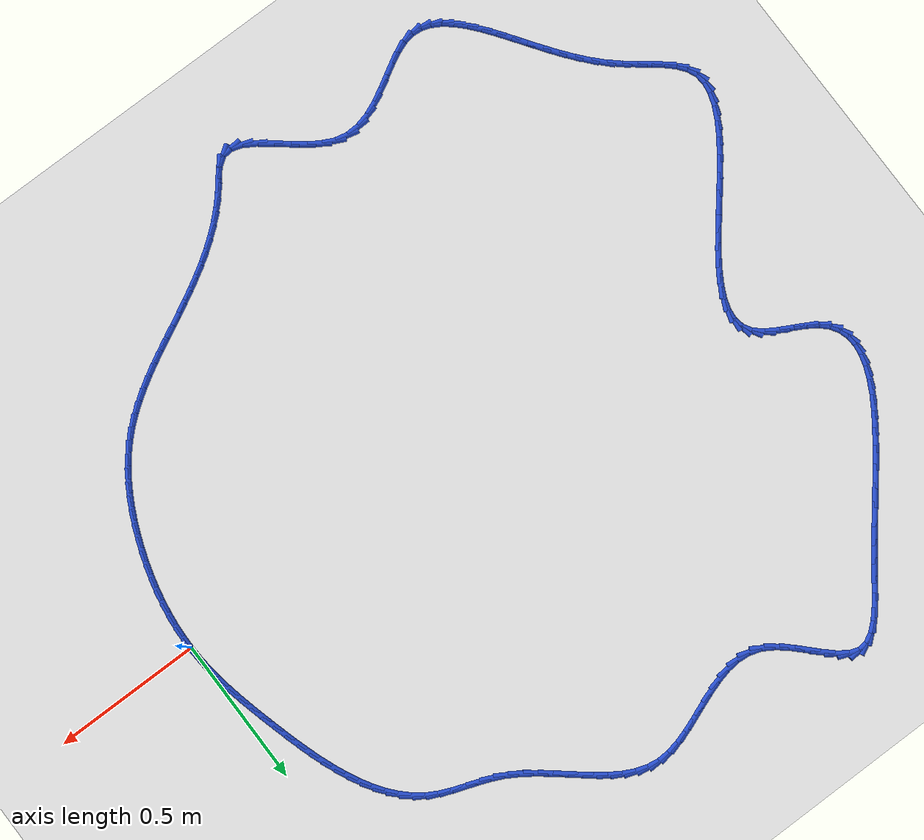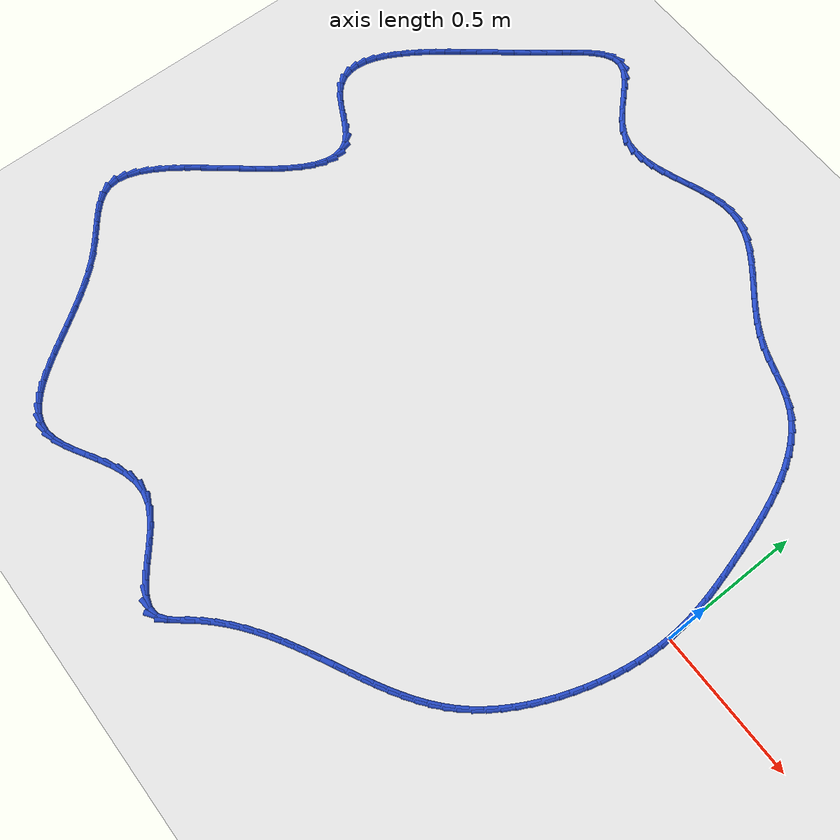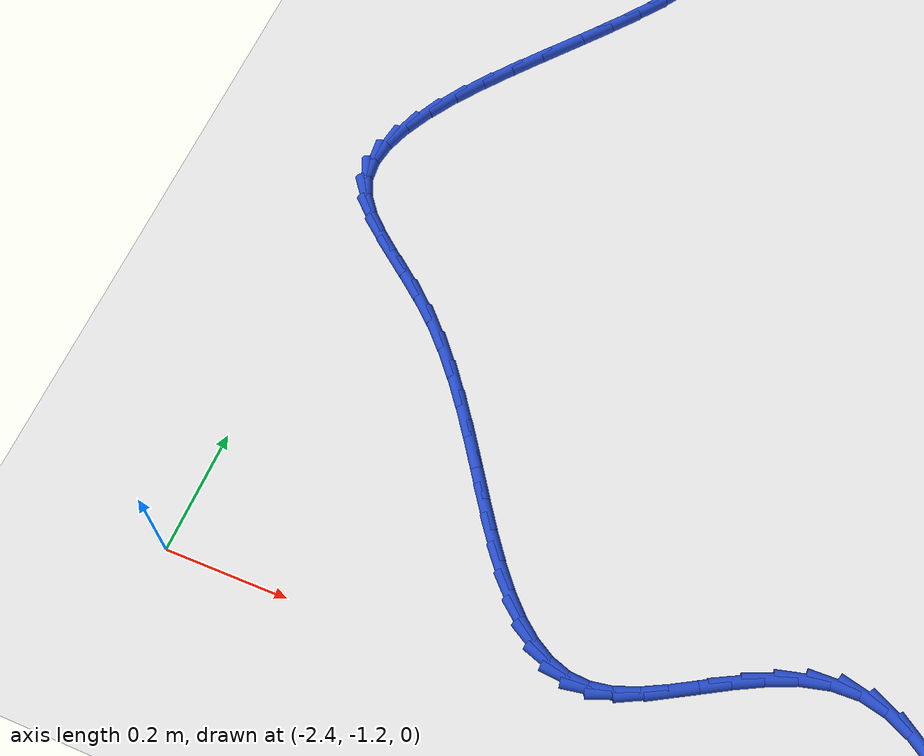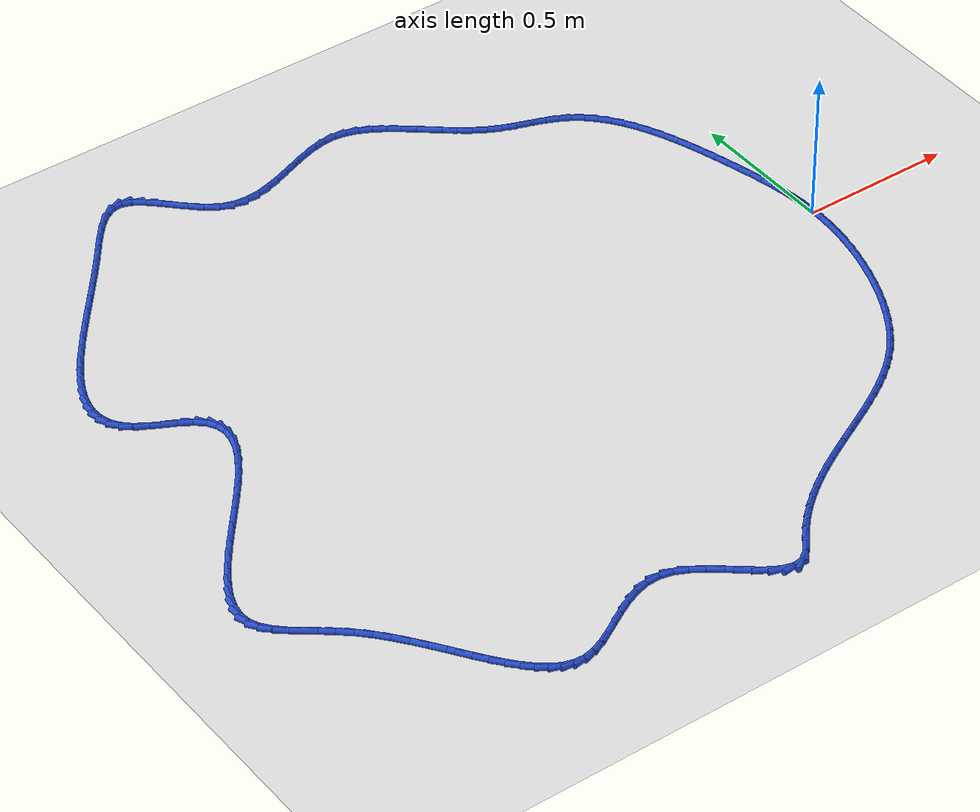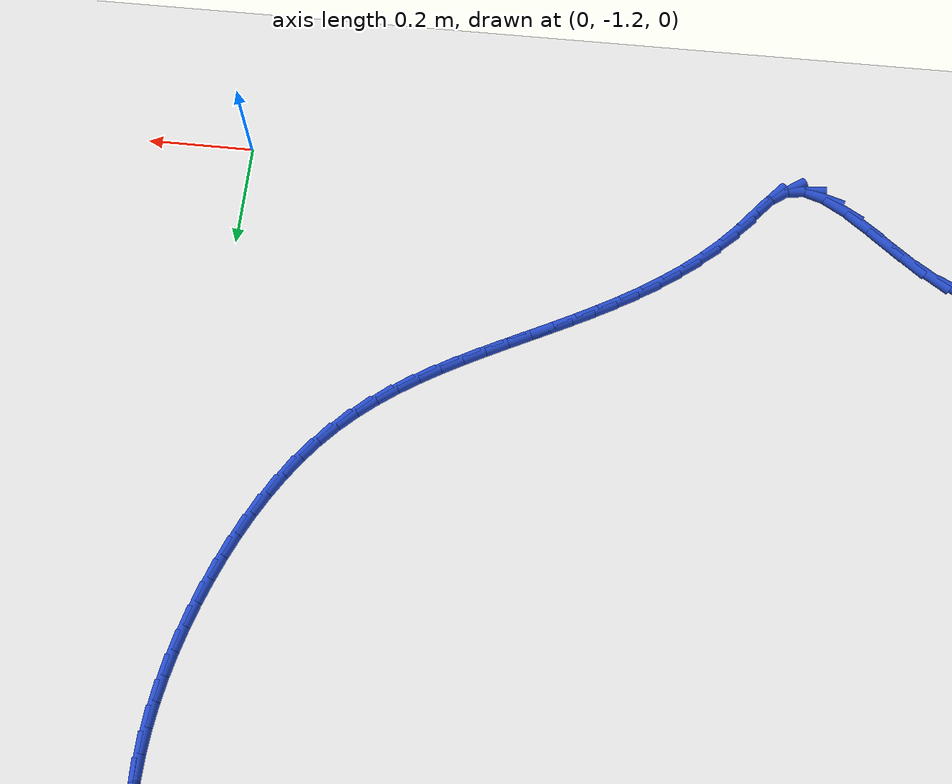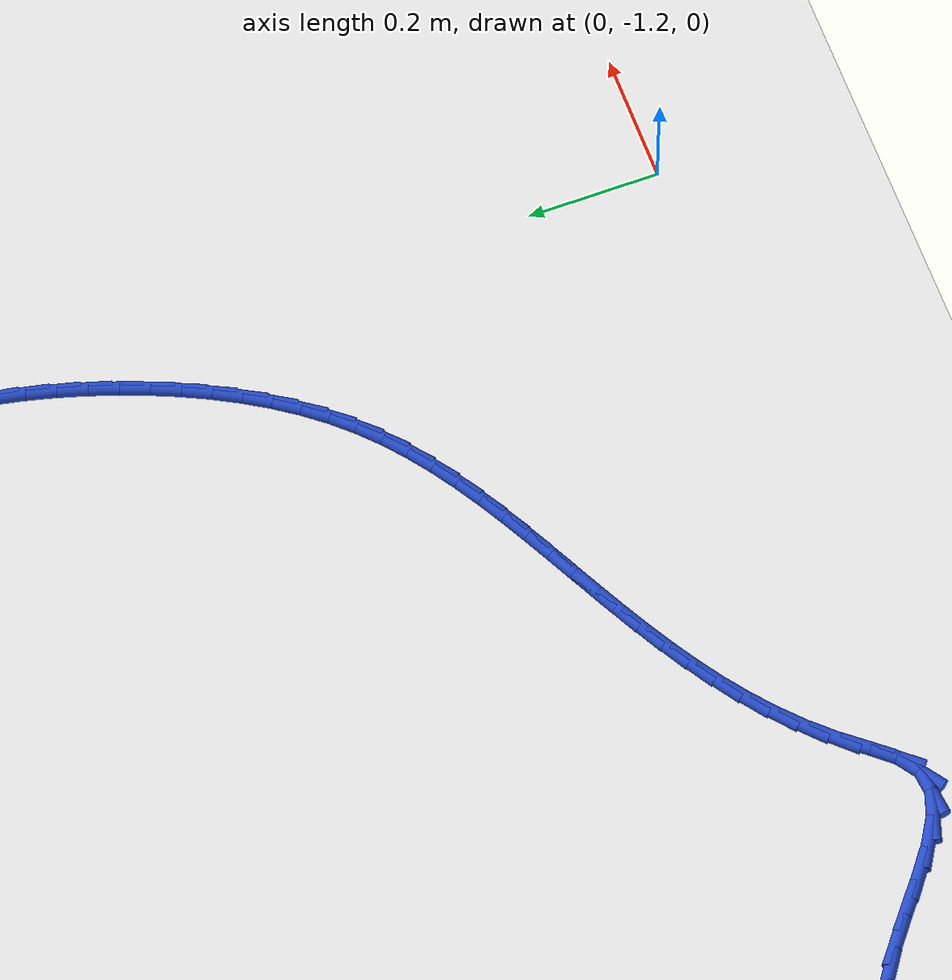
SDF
<sdf version="1.6">
 <world name="default">
  <light name="sun" type="directional">
   <pose>0 0 10 0 -0 0</pose>
   <diffuse>0.8 0.8 0.8 1</diffuse>
   <specular>0.2 0.2 0.2 1</specular>
   <attenuation>
    <range>1000</range>
    <constant>0.9</constant>
    <linear>0.01</linear>
    <quadratic>0.001</quadratic>
   </attenuation>
   <direction>-0.5 0.1 -0.9</direction>
  </light>
  <model name="ground_plane">
   <static>1</static>
   <link name="link">
    <collision name="collision">
     <geometry><plane><normal>0 0 1</normal><size>100 100</size></plane></geometry>
     <surface><friction><ode><mu>100</mu><mu2>50</mu2></ode></friction></surface>
    </collision>
    <visual name="visual">
     <cast_shadows>0</cast_shadows>
     <geometry><plane><normal>0 0 1</normal><size>100 100</size></plane></geometry>
     <material>
      <script><uri>file://media/materials/scripts/gazebo.material</uri><name>Gazebo/WhiteGlow</name></script>
     </material>
    </visual>
   </link>
  </model>
  <gravity>0 0 -9.8</gravity>
  <magnetic_field>6e-06 2.3e-05 -4.2e-05</magnetic_field>
  <atmosphere type="adiabatic"/>
  <physics name="default_physics" default="0" type="ode">
   <max_step_size>0.001</max_step_size>
   <real_time_factor>1</real_time_factor>
   <real_time_update_rate>1000</real_time_update_rate>
  </physics>
  <scene><ambient>0.4 0.4 0.4 1</ambient><background>0.7 0.7 0.7 1</background><shadows>1</shadows></scene>
  <spherical_coordinates>
   <surface_model>EARTH_WGS84</surface_model>
   <latitude_deg>0</latitude_deg>
   <longitude_deg>0</longitude_deg>
   <elevation>0</elevation>
   <heading_deg>0</heading_deg>
  </spherical_coordinates>
  <model name="line">
   <link name="link_0">
    <pose>-1.214306433183765e-17 6.938893903907228e-18 0.01 0 1.57 -1.5278417276715544</pose>
    <collision name="collision">
     <geometry><cylinder><radius>0.01</radius><length>0.08</length></cylinder></geometry>
    </collision>
    <visual name="visual">
     <material>
      <script><name>Gazebo/Blue</name><uri>file://media/materials/scripts/gazebo.material</uri></script>
     </material>
     <geometry><cylinder><radius>0.01</radius><length>0.08</length></cylinder></geometry>
    </visual>
   </link>
   <link name="link_1">
    <pose>-0.001841011206535081 0.042833103393000345 0.01 0 1.57 -1.4783494542227635</pose>
    <collision name="collision">
     <geometry><cylinder><radius>0.01</radius><length>0.08</length></cylinder></geometry>
    </collision>
    <visual name="visual">
     <material>
      <script><name>Gazebo/Blue</name><uri>file://media/materials/scripts/gazebo.material</uri></script>
     </material>
     <geometry><cylinder><radius>0.01</radius><length>0.08</length></cylinder></geometry>
    </visual>
   </link>
   <link name="link_2">
    <pose>-0.005796762681849369 0.0855005918954934 0.01 0 1.57 -1.434578861854866</pose>
    <collision name="collision">
     <geometry><cylinder><radius>0.01</radius><length>0.08</length></cylinder></geometry>
    </collision>
    <visual name="visual">
     <material>
      <script><name>Gazebo/Blue</name><uri>file://media/materials/scripts/gazebo.material</uri></script>
     </material>
     <geometry><cylinder><radius>0.01</radius><length>0.08</length></cylinder></geometry>
    </visual>
   </link>
   <link name="link_3">
    <pose>-0.0116405768046681 0.12813554299801427 0.01 0 1.57 -1.3969493244081939</pose>
    <collision name="collision">
     <geometry><cylinder><radius>0.01</radius><length>0.08</length></cylinder></geometry>
    </collision>
    <visual name="visual">
     <material>
      <script><name>Gazebo/Blue</name><uri>file://media/materials/scripts/gazebo.material</uri></script>
     </material>
     <geometry><cylinder><radius>0.01</radius><length>0.08</length></cylinder></geometry>
    </visual>
   </link>
   <link name="link_4">
    <pose>-0.019145775953716537 0.17087103419109848 0.01 0 1.57 -1.3656684076454348</pose>
    <collision name="collision">
     <geometry><cylinder><radius>0.01</radius><length>0.08</length></cylinder></geometry>
    </collision>
    <visual name="visual">
     <material>
      <script><name>Gazebo/Blue</name><uri>file://media/materials/scripts/gazebo.material</uri></script>
     </material>
     <geometry><cylinder><radius>0.01</radius><length>0.08</length></cylinder></geometry>
    </visual>
   </link>
   <link name="link_5">
    <pose>-0.028085682507719905 0.213840142965281 0.01 0 1.57 -1.3407712673327594</pose>
    <collision name="collision">
     <geometry><cylinder><radius>0.01</radius><length>0.08</length></cylinder></geometry>
    </collision>
    <visual name="visual">
     <material>
      <script><name>Gazebo/Blue</name><uri>file://media/materials/scripts/gazebo.material</uri></script>
     </material>
     <geometry><cylinder><radius>0.01</radius><length>0.08</length></cylinder></geometry>
    </visual>
   </link>
   <link name="link_6">
    <pose>-0.03823361884540343 0.25717594681109707 0.01 0 1.57 -1.3221625516908762</pose>
    <collision name="collision">
     <geometry><cylinder><radius>0.01</radius><length>0.08</length></cylinder></geometry>
    </collision>
    <visual name="visual">
     <material>
      <script><name>Gazebo/Blue</name><uri>file://media/materials/scripts/gazebo.material</uri></script>
     </material>
     <geometry><cylinder><radius>0.01</radius><length>0.08</length></cylinder></geometry>
    </visual>
   </link>
   <link name="link_7">
    <pose>-0.049362907345492396 0.30101152321908214 0.01 0 1.57 -1.3096531524751374</pose>
    <collision name="collision">
     <geometry><cylinder><radius>0.01</radius><length>0.08</length></cylinder></geometry>
    </collision>
    <visual name="visual">
     <material>
      <script><name>Gazebo/Blue</name><uri>file://media/materials/scripts/gazebo.material</uri></script>
     </material>
     <geometry><cylinder><radius>0.01</radius><length>0.08</length></cylinder></geometry>
    </visual>
   </link>
   <link name="link_8">
    <pose>-0.06124690448104832 0.3454799068336491 0.01 0 1.57 -1.3004330214131437</pose>
    <collision name="collision">
     <geometry><cylinder><radius>0.01</radius><length>0.08</length></cylinder></geometry>
    </collision>
    <visual name="visual">
     <material>
      <script><name>Gazebo/Blue</name><uri>file://media/materials/scripts/gazebo.material</uri></script>
     </material>
     <geometry><cylinder><radius>0.01</radius><length>0.08</length></cylinder></geometry>
    </visual>
   </link>
   <link name="link_9">
    <pose>-0.07375135922839249 0.3905980232646502 0.01 0 1.57 -1.286233361920139</pose>
    <collision name="collision">
     <geometry><cylinder><radius>0.01</radius><length>0.08</length></cylinder></geometry>
    </collision>
    <visual name="visual">
     <material>
      <script><name>Gazebo/Blue</name><uri>file://media/materials/scripts/gazebo.material</uri></script>
     </material>
     <geometry><cylinder><radius>0.01</radius><length>0.08</length></cylinder></geometry>
    </visual>
   </link>
   <link name="link_10">
    <pose>-0.08703555744562069 0.4360139123060065 0.01 0 1.57 -1.2653246378833036</pose>
    <collision name="collision">
     <geometry><cylinder><radius>0.01</radius><length>0.08</length></cylinder></geometry>
    </collision>
    <visual name="visual">
     <material>
      <script><name>Gazebo/Blue</name><uri>file://media/materials/scripts/gazebo.material</uri></script>
     </material>
     <geometry><cylinder><radius>0.01</radius><length>0.08</length></cylinder></geometry>
    </visual>
   </link>
   <link name="link_11">
    <pose>-0.10131694668544898 0.48130252234300114 0.01 0 1.57 -1.2373445891181185</pose>
    <collision name="collision">
     <geometry><cylinder><radius>0.01</radius><length>0.08</length></cylinder></geometry>
    </collision>
    <visual name="visual">
     <material>
      <script><name>Gazebo/Blue</name><uri>file://media/materials/scripts/gazebo.material</uri></script>
     </material>
     <geometry><cylinder><radius>0.01</radius><length>0.08</length></cylinder></geometry>
    </visual>
   </link>
   <link name="link_12">
    <pose>-0.11681297450059346 0.5260388017609174 0.01 0 1.57 -1.2016776090968448</pose>
    <collision name="collision">
     <geometry><cylinder><radius>0.01</radius><length>0.08</length></cylinder></geometry>
    </collision>
    <visual name="visual">
     <material>
      <script><name>Gazebo/Blue</name><uri>file://media/materials/scripts/gazebo.material</uri></script>
     </material>
     <geometry><cylinder><radius>0.01</radius><length>0.08</length></cylinder></geometry>
    </visual>
   </link>
   <link name="link_13">
    <pose>-0.1337410884437702 0.5697976989450391 0.01 0 1.57 -1.157460944009564</pose>
    <collision name="collision">
     <geometry><cylinder><radius>0.01</radius><length>0.08</length></cylinder></geometry>
    </collision>
    <visual name="visual">
     <material>
      <script><name>Gazebo/Blue</name><uri>file://media/materials/scripts/gazebo.material</uri></script>
     </material>
     <geometry><cylinder><radius>0.01</radius><length>0.08</length></cylinder></geometry>
    </visual>
   </link>
   <link name="link_14">
    <pose>-0.15231873606769528 0.612154162280649 0.01 0 1.57 -1.1035992679864668</pose>
    <collision name="collision">
     <geometry><cylinder><radius>0.01</radius><length>0.08</length></cylinder></geometry>
    </collision>
    <visual name="visual">
     <material>
      <script><name>Gazebo/Blue</name><uri>file://media/materials/scripts/gazebo.material</uri></script>
     </material>
     <geometry><cylinder><radius>0.01</radius><length>0.08</length></cylinder></geometry>
    </visual>
   </link>
   <link name="link_15">
    <pose>-0.17276336492508484 0.652683140153031 0.01 0 1.57 -1.0388101880823821</pose>
    <collision name="collision">
     <geometry><cylinder><radius>0.01</radius><length>0.08</length></cylinder></geometry>
    </collision>
    <visual name="visual">
     <material>
      <script><name>Gazebo/Blue</name><uri>file://media/materials/scripts/gazebo.material</uri></script>
     </material>
     <geometry><cylinder><radius>0.01</radius><length>0.08</length></cylinder></geometry>
    </visual>
   </link>
   <link name="link_16">
    <pose>-0.19529242256865492 0.6909595809474681 0.01 0 1.57 -0.9617363035974724</pose>
    <collision name="collision">
     <geometry><cylinder><radius>0.01</radius><length>0.08</length></cylinder></geometry>
    </collision>
    <visual name="visual">
     <material>
      <script><name>Gazebo/Blue</name><uri>file://media/materials/scripts/gazebo.material</uri></script>
     </material>
     <geometry><cylinder><radius>0.01</radius><length>0.08</length></cylinder></geometry>
    </visual>
   </link>
   <link name="link_17">
    <pose>-0.2201233565511216 0.7265584330492438 0.01 0 1.57 -0.8711731067692097</pose>
    <collision name="collision">
     <geometry><cylinder><radius>0.01</radius><length>0.08</length></cylinder></geometry>
    </collision>
    <visual name="visual">
     <material>
      <script><name>Gazebo/Blue</name><uri>file://media/materials/scripts/gazebo.material</uri></script>
     </material>
     <geometry><cylinder><radius>0.01</radius><length>0.08</length></cylinder></geometry>
    </visual>
   </link>
   <link name="link_18">
    <pose>-0.24747361442520116 0.7590546448436418 0.01 0 1.57 -0.7664604726029305</pose>
    <collision name="collision">
     <geometry><cylinder><radius>0.01</radius><length>0.08</length></cylinder></geometry>
    </collision>
    <visual name="visual">
     <material>
      <script><name>Gazebo/Blue</name><uri>file://media/materials/scripts/gazebo.material</uri></script>
     </material>
     <geometry><cylinder><radius>0.01</radius><length>0.08</length></cylinder></geometry>
    </visual>
   </link>
   <link name="link_19">
    <pose>-0.27756064374360934 0.7880231647159448 0.01 0 1.57 -0.6480344007831891</pose>
    <collision name="collision">
     <geometry><cylinder><radius>0.01</radius><length>0.08</length></cylinder></geometry>
    </collision>
    <visual name="visual">
     <material>
      <script><name>Gazebo/Blue</name><uri>file://media/materials/scripts/gazebo.material</uri></script>
     </material>
     <geometry><cylinder><radius>0.01</radius><length>0.08</length></cylinder></geometry>
    </visual>
   </link>
   <link name="link_20">
    <pose>-0.31060189205906247 0.8130389410514363 0.01 0 1.57 -0.519145211485778</pose>
    <collision name="collision">
     <geometry><cylinder><radius>0.01</radius><length>0.08</length></cylinder></geometry>
    </collision>
    <visual name="visual">
     <material>
      <script><name>Gazebo/Blue</name><uri>file://media/materials/scripts/gazebo.material</uri></script>
     </material>
     <geometry><cylinder><radius>0.01</radius><length>0.08</length></cylinder></geometry>
    </visual>
   </link>
   <link name="link_21">
    <pose>-0.3467924018624729 0.8337191890281186 0.01 0 1.57 -0.410825268227258</pose>
    <collision name="collision">
     <geometry><cylinder><radius>0.01</radius><length>0.08</length></cylinder></geometry>
    </collision>
    <visual name="visual">
     <material>
      <script><name>Gazebo/Blue</name><uri>file://media/materials/scripts/gazebo.material</uri></script>
     </material>
     <geometry><cylinder><radius>0.01</radius><length>0.08</length></cylinder></geometry>
    </visual>
   </link>
   <link name="link_22">
    <pose>-0.3857846314451838 0.8507047002861361 0.01 0 1.57 -0.3512769107563529</pose>
    <collision name="collision">
     <geometry><cylinder><radius>0.01</radius><length>0.08</length></cylinder></geometry>
    </collision>
    <visual name="visual">
     <material>
      <script><name>Gazebo/Blue</name><uri>file://media/materials/scripts/gazebo.material</uri></script>
     </material>
     <geometry><cylinder><radius>0.01</radius><length>0.08</length></cylinder></geometry>
    </visual>
   </link>
   <link name="link_23">
    <pose>-0.4266728593593721 0.8656892636651663 0.01 0 1.57 -0.33831316836929326</pose>
    <collision name="collision">
     <geometry><cylinder><radius>0.01</radius><length>0.08</length></cylinder></geometry>
    </collision>
    <visual name="visual">
     <material>
      <script><name>Gazebo/Blue</name><uri>file://media/materials/scripts/gazebo.material</uri></script>
     </material>
     <geometry><cylinder><radius>0.01</radius><length>0.08</length></cylinder></geometry>
    </visual>
   </link>
   <link name="link_24">
    <pose>-0.4685258392022841 0.8804148204263631 0.01 0 1.57 -0.3692167166954547</pose>
    <collision name="collision">
     <geometry><cylinder><radius>0.01</radius><length>0.08</length></cylinder></geometry>
    </collision>
    <visual name="visual">
     <material>
      <script><name>Gazebo/Blue</name><uri>file://media/materials/scripts/gazebo.material</uri></script>
     </material>
     <geometry><cylinder><radius>0.01</radius><length>0.08</length></cylinder></geometry>
    </visual>
   </link>
   <link name="link_25">
    <pose>-0.5104123245711665 0.8966233118308796 0.01 0 1.57 -0.44263984575909476</pose>
    <collision name="collision">
     <geometry><cylinder><radius>0.01</radius><length>0.08</length></cylinder></geometry>
    </collision>
    <visual name="visual">
     <material>
      <script><name>Gazebo/Blue</name><uri>file://media/materials/scripts/gazebo.material</uri></script>
     </material>
     <geometry><cylinder><radius>0.01</radius><length>0.08</length></cylinder></geometry>
    </visual>
   </link>
   <link name="link_26">
    <pose>-0.5514025981996287 0.9160530898649593 0.01 0 1.57 -0.5382495665432401</pose>
    <collision name="collision">
     <geometry><cylinder><radius>0.01</radius><length>0.08</length></cylinder></geometry>
    </collision>
    <visual name="visual">
     <material>
      <script><name>Gazebo/Blue</name><uri>file://media/materials/scripts/gazebo.material</uri></script>
     </material>
     <geometry><cylinder><radius>0.01</radius><length>0.08</length></cylinder></geometry>
    </visual>
   </link>
   <link name="link_27">
    <pose>-0.5909086997709394 0.9396403153730617 0.01 0 1.57 -0.6129470023603767</pose>
    <collision name="collision">
     <geometry><cylinder><radius>0.01</radius><length>0.08</length></cylinder></geometry>
    </collision>
    <visual name="visual">
     <material>
      <script><name>Gazebo/Blue</name><uri>file://media/materials/scripts/gazebo.material</uri></script>
     </material>
     <geometry><cylinder><radius>0.01</radius><length>0.08</length></cylinder></geometry>
    </visual>
   </link>
   <link name="link_28">
    <pose>-0.6291139935760048 0.9665106526806941 0.01 0 1.57 -0.6627587824089363</pose>
    <collision name="collision">
     <geometry><cylinder><radius>0.01</radius><length>0.08</length></cylinder></geometry>
    </collision>
    <visual name="visual">
     <material>
      <script><name>Gazebo/Blue</name><uri>file://media/materials/scripts/gazebo.material</uri></script>
     </material>
     <geometry><cylinder><radius>0.01</radius><length>0.08</length></cylinder></geometry>
    </visual>
   </link>
   <link name="link_29">
    <pose>-0.6663075899000868 0.9955415531654309 0.01 0 1.57 -0.6894790888531099</pose>
    <collision name="collision">
     <geometry><cylinder><radius>0.01</radius><length>0.08</length></cylinder></geometry>
    </collision>
    <visual name="visual">
     <material>
      <script><name>Gazebo/Blue</name><uri>file://media/materials/scripts/gazebo.material</uri></script>
     </material>
     <geometry><cylinder><radius>0.01</radius><length>0.08</length></cylinder></geometry>
    </visual>
   </link>
   <link name="link_30">
    <pose>-0.7027785990284473 1.0256104682048464 0.01 0 1.57 -0.6939698003422797</pose>
    <collision name="collision">
     <geometry><cylinder><radius>0.01</radius><length>0.08</length></cylinder></geometry>
    </collision>
    <visual name="visual">
     <material>
      <script><name>Gazebo/Blue</name><uri>file://media/materials/scripts/gazebo.material</uri></script>
     </material>
     <geometry><cylinder><radius>0.01</radius><length>0.08</length></cylinder></geometry>
    </visual>
   </link>
   <link name="link_31">
    <pose>-0.7388161312463483 1.0555948491765144 0.01 0 1.57 -0.6758063038308365</pose>
    <collision name="collision">
     <geometry><cylinder><radius>0.01</radius><length>0.08</length></cylinder></geometry>
    </collision>
    <visual name="visual">
     <material>
      <script><name>Gazebo/Blue</name><uri>file://media/materials/scripts/gazebo.material</uri></script>
     </material>
     <geometry><cylinder><radius>0.01</radius><length>0.08</length></cylinder></geometry>
    </visual>
   </link>
   <link name="link_32">
    <pose>-0.774709296839052 1.0843721474580104 0.01 0 1.57 -0.6331072297800732</pose>
    <collision name="collision">
     <geometry><cylinder><radius>0.01</radius><length>0.08</length></cylinder></geometry>
    </collision>
    <visual name="visual">
     <material>
      <script><name>Gazebo/Blue</name><uri>file://media/materials/scripts/gazebo.material</uri></script>
     </material>
     <geometry><cylinder><radius>0.01</radius><length>0.08</length></cylinder></geometry>
    </visual>
   </link>
   <link name="link_33">
    <pose>-0.8107472060918199 1.1108198144269077 0.01 0 1.57 -0.5625453900071486</pose>
    <collision name="collision">
     <geometry><cylinder><radius>0.01</radius><length>0.08</length></cylinder></geometry>
    </collision>
    <visual name="visual">
     <material>
      <script><name>Gazebo/Blue</name><uri>file://media/materials/scripts/gazebo.material</uri></script>
     </material>
     <geometry><cylinder><radius>0.01</radius><length>0.08</length></cylinder></geometry>
    </visual>
   </link>
   <link name="link_34">
    <pose>-0.8472189692899144 1.1338153014607824 0.01 0 1.57 -0.45984189885413</pose>
    <collision name="collision">
     <geometry><cylinder><radius>0.01</radius><length>0.08</length></cylinder></geometry>
    </collision>
    <visual name="visual">
     <material>
      <script><name>Gazebo/Blue</name><uri>file://media/materials/scripts/gazebo.material</uri></script>
     </material>
     <geometry><cylinder><radius>0.01</radius><length>0.08</length></cylinder></geometry>
    </visual>
   </link>
   <link name="link_35">
    <pose>-0.884413696718597 1.1522360599372066 0.01 0 1.57 -0.3214650436060106</pose>
    <collision name="collision">
     <geometry><cylinder><radius>0.01</radius><length>0.08</length></cylinder></geometry>
    </collision>
    <visual name="visual">
     <material>
      <script><name>Gazebo/Blue</name><uri>file://media/materials/scripts/gazebo.material</uri></script>
     </material>
     <geometry><cylinder><radius>0.01</radius><length>0.08</length></cylinder></geometry>
    </visual>
   </link>
   <link name="link_36">
    <pose>-0.9226204986631302 1.1649595412337561 0.01 0 1.57 -0.14833187525414215</pose>
    <collision name="collision">
     <geometry><cylinder><radius>0.01</radius><length>0.08</length></cylinder></geometry>
    </collision>
    <visual name="visual">
     <material>
      <script><name>Gazebo/Blue</name><uri>file://media/materials/scripts/gazebo.material</uri></script>
     </material>
     <geometry><cylinder><radius>0.01</radius><length>0.08</length></cylinder></geometry>
    </visual>
   </link>
   <link name="link_37">
    <pose>-0.9621284854087759 1.1708631967280052 0.01 0 1.57 0.042862806113985</pose>
    <collision name="collision">
     <geometry><cylinder><radius>0.01</radius><length>0.08</length></cylinder></geometry>
    </collision>
    <visual name="visual">
     <material>
      <script><name>Gazebo/Blue</name><uri>file://media/materials/scripts/gazebo.material</uri></script>
     </material>
     <geometry><cylinder><radius>0.01</radius><length>0.08</length></cylinder></geometry>
    </visual>
   </link>
   <link name="link_38">
    <pose>-1.003168622253646 1.169103023225407 0.01 0 1.57 0.19530432509419043</pose>
    <collision name="collision">
     <geometry><cylinder><radius>0.01</radius><length>0.08</length></cylinder></geometry>
    </collision>
    <visual name="visual">
     <material>
      <script><name>Gazebo/Blue</name><uri>file://media/materials/scripts/gazebo.material</uri></script>
     </material>
     <geometry><cylinder><radius>0.01</radius><length>0.08</length></cylinder></geometry>
    </visual>
   </link>
   <link name="link_39">
    <pose>-1.0455798597353239 1.1607129768286568 0.01 0 1.57 0.29508999515194</pose>
    <collision name="collision">
     <geometry><cylinder><radius>0.01</radius><length>0.08</length></cylinder></geometry>
    </collision>
    <visual name="visual">
     <material>
      <script><name>Gazebo/Blue</name><uri>file://media/materials/scripts/gazebo.material</uri></script>
     </material>
     <geometry><cylinder><radius>0.01</radius><length>0.08</length></cylinder></geometry>
    </visual>
   </link>
   <link name="link_40">
    <pose>-1.0890391896587786 1.1475028821492694 0.01 0 1.57 0.3517859616980934</pose>
    <collision name="collision">
     <geometry><cylinder><radius>0.01</radius><length>0.08</length></cylinder></geometry>
    </collision>
    <visual name="visual">
     <material>
      <script><name>Gazebo/Blue</name><uri>file://media/materials/scripts/gazebo.material</uri></script>
     </material>
     <geometry><cylinder><radius>0.01</radius><length>0.08</length></cylinder></geometry>
    </visual>
   </link>
   <link name="link_41">
    <pose>-1.1332230921506417 1.1312850150102483 0.01 0 1.57 0.37234718192794997</pose>
    <collision name="collision">
     <geometry><cylinder><radius>0.01</radius><length>0.08</length></cylinder></geometry>
    </collision>
    <visual name="visual">
     <material>
      <script><name>Gazebo/Blue</name><uri>file://media/materials/scripts/gazebo.material</uri></script>
     </material>
     <geometry><cylinder><radius>0.01</radius><length>0.08</length></cylinder></geometry>
    </visual>
   </link>
   <link name="link_42">
    <pose>-1.1778080473375483 1.1138716512345963 0.01 0 1.57 0.3597155374420773</pose>
    <collision name="collision">
     <geometry><cylinder><radius>0.01</radius><length>0.08</length></cylinder></geometry>
    </collision>
    <visual name="visual">
     <material>
      <script><name>Gazebo/Blue</name><uri>file://media/materials/scripts/gazebo.material</uri></script>
     </material>
     <geometry><cylinder><radius>0.01</radius><length>0.08</length></cylinder></geometry>
    </visual>
   </link>
   <link name="link_43">
    <pose>-1.222470535346131 1.0970750666453168 0.01 0 1.57 0.31284997226879246</pose>
    <collision name="collision">
     <geometry><cylinder><radius>0.01</radius><length>0.08</length></cylinder></geometry>
    </collision>
    <visual name="visual">
     <material>
      <script><name>Gazebo/Blue</name><uri>file://media/materials/scripts/gazebo.material</uri></script>
     </material>
     <geometry><cylinder><radius>0.01</radius><length>0.08</length></cylinder></geometry>
    </visual>
   </link>
   <link name="link_44">
    <pose>-1.2668870363030231 1.0827075370654127 0.01 0 1.57 0.22696474305754447</pose>
    <collision name="collision">
     <geometry><cylinder><radius>0.01</radius><length>0.08</length></cylinder></geometry>
    </collision>
    <visual name="visual">
     <material>
      <script><name>Gazebo/Blue</name><uri>file://media/materials/scripts/gazebo.material</uri></script>
     </material>
     <geometry><cylinder><radius>0.01</radius><length>0.08</length></cylinder></geometry>
    </visual>
   </link>
   <link name="link_45">
    <pose>-1.3107340303348591 1.0725813383178884 0.01 0 1.57 0.09453035985875118</pose>
    <collision name="collision">
     <geometry><cylinder><radius>0.01</radius><length>0.08</length></cylinder></geometry>
    </collision>
    <visual name="visual">
     <material>
      <script><name>Gazebo/Blue</name><uri>file://media/materials/scripts/gazebo.material</uri></script>
     </material>
     <geometry><cylinder><radius>0.01</radius><length>0.08</length></cylinder></geometry>
    </visual>
   </link>
   <link name="link_46">
    <pose>-1.3536879975682719 1.068508746225746 0.01 0 1.57 -0.09063563532409251</pose>
    <collision name="collision">
     <geometry><cylinder><radius>0.01</radius><length>0.08</length></cylinder></geometry>
    </collision>
    <visual name="visual">
     <material>
      <script><name>Gazebo/Blue</name><uri>file://media/materials/scripts/gazebo.material</uri></script>
     </material>
     <geometry><cylinder><radius>0.01</radius><length>0.08</length></cylinder></geometry>
    </visual>
   </link>
   <link name="link_47">
    <pose>-1.395425418129895 1.07230203661199 0.01 0 1.57 -0.32336743059411904</pose>
    <collision name="collision">
     <geometry><cylinder><radius>0.01</radius><length>0.08</length></cylinder></geometry>
    </collision>
    <visual name="visual">
     <material>
      <script><name>Gazebo/Blue</name><uri>file://media/materials/scripts/gazebo.material</uri></script>
     </material>
     <geometry><cylinder><radius>0.01</radius><length>0.08</length></cylinder></geometry>
    </visual>
   </link>
   <link name="link_48">
    <pose>-1.4356227790329081 1.0857734116472186 0.01 0 1.57 -0.5563269946003826</pose>
    <collision name="collision">
     <geometry><cylinder><radius>0.01</radius><length>0.08</length></cylinder></geometry>
    </collision>
    <visual name="visual">
     <material>
      <script><name>Gazebo/Blue</name><uri>file://media/materials/scripts/gazebo.material</uri></script>
     </material>
     <geometry><cylinder><radius>0.01</radius><length>0.08</length></cylinder></geometry>
    </visual>
   </link>
   <link name="link_49">
    <pose>-1.4740558877256191 1.1096728300561989 0.01 0 1.57 -0.7055172911564553</pose>
    <collision name="collision">
     <geometry><cylinder><radius>0.01</radius><length>0.08</length></cylinder></geometry>
    </collision>
    <visual name="visual">
     <material>
      <script><name>Gazebo/Blue</name><uri>file://media/materials/scripts/gazebo.material</uri></script>
     </material>
     <geometry><cylinder><radius>0.01</radius><length>0.08</length></cylinder></geometry>
    </visual>
   </link>
   <link name="link_50">
    <pose>-1.5108500111330263 1.1410127413771438 0.01 0 1.57 -0.7799104085364337</pose>
    <collision name="collision">
     <geometry><cylinder><radius>0.01</radius><length>0.08</length></cylinder></geometry>
    </collision>
    <visual name="visual">
     <material>
      <script><name>Gazebo/Blue</name><uri>file://media/materials/scripts/gazebo.material</uri></script>
     </material>
     <geometry><cylinder><radius>0.01</radius><length>0.08</length></cylinder></geometry>
    </visual>
   </link>
   <link name="link_51">
    <pose>-1.5462072344220585 1.1759840152397094 0.01 0 1.57 -0.7951357761220991</pose>
    <collision name="collision">
     <geometry><cylinder><radius>0.01</radius><length>0.08</length></cylinder></geometry>
    </collision>
    <visual name="visual">
     <material>
      <script><name>Gazebo/Blue</name><uri>file://media/materials/scripts/gazebo.material</uri></script>
     </material>
     <geometry><cylinder><radius>0.01</radius><length>0.08</length></cylinder></geometry>
    </visual>
   </link>
   <link name="link_52">
    <pose>-1.580329642759644 1.2107775212735508 0.01 0 1.57 -0.749682474816004</pose>
    <collision name="collision">
     <geometry><cylinder><radius>0.01</radius><length>0.08</length></cylinder></geometry>
    </collision>
    <visual name="visual">
     <material>
      <script><name>Gazebo/Blue</name><uri>file://media/materials/scripts/gazebo.material</uri></script>
     </material>
     <geometry><cylinder><radius>0.01</radius><length>0.08</length></cylinder></geometry>
    </visual>
   </link>
   <link name="link_53">
    <pose>-1.6134193213127122 1.2415841291083227 0.01 0 1.57 -0.6196008008630823</pose>
    <collision name="collision">
     <geometry><cylinder><radius>0.01</radius><length>0.08</length></cylinder></geometry>
    </collision>
    <visual name="visual">
     <material>
      <script><name>Gazebo/Blue</name><uri>file://media/materials/scripts/gazebo.material</uri></script>
     </material>
     <geometry><cylinder><radius>0.01</radius><length>0.08</length></cylinder></geometry>
    </visual>
   </link>
   <link name="link_54">
    <pose>-1.64567835524819 1.2645947083736808 0.01 0 1.57 -0.3460718468006396</pose>
    <collision name="collision">
     <geometry><cylinder><radius>0.01</radius><length>0.08</length></cylinder></geometry>
    </collision>
    <visual name="visual">
     <material>
      <script><name>Gazebo/Blue</name><uri>file://media/materials/scripts/gazebo.material</uri></script>
     </material>
     <geometry><cylinder><radius>0.01</radius><length>0.08</length></cylinder></geometry>
    </visual>
   </link>
   <link name="link_55">
    <pose>-1.6773088297330074 1.276000128699281 0.01 0 1.57 0.09871644941660133</pose>
    <collision name="collision">
     <geometry><cylinder><radius>0.01</radius><length>0.08</length></cylinder></geometry>
    </collision>
    <visual name="visual">
     <material>
      <script><name>Gazebo/Blue</name><uri>file://media/materials/scripts/gazebo.material</uri></script>
     </material>
     <geometry><cylinder><radius>0.01</radius><length>0.08</length></cylinder></geometry>
    </visual>
   </link>
   <link name="link_56">
    <pose>-1.7085328754849136 1.2729077502227597 0.01 0 1.57 0.4836306630999242</pose>
    <collision name="collision">
     <geometry><cylinder><radius>0.01</radius><length>0.08</length></cylinder></geometry>
    </collision>
    <visual name="visual">
     <material>
      <script><name>Gazebo/Blue</name><uri>file://media/materials/scripts/gazebo.material</uri></script>
     </material>
     <geometry><cylinder><radius>0.01</radius><length>0.08</length></cylinder></geometry>
    </visual>
   </link>
   <link name="link_57">
    <pose>-1.7396630031520222 1.2565571392268893 0.01 0 1.57 0.7143501030441997</pose>
    <collision name="collision">
     <geometry><cylinder><radius>0.01</radius><length>0.08</length></cylinder></geometry>
    </collision>
    <visual name="visual">
     <material>
      <script><name>Gazebo/Blue</name><uri>file://media/materials/scripts/gazebo.material</uri></script>
     </material>
     <geometry><cylinder><radius>0.01</radius><length>0.08</length></cylinder></geometry>
    </visual>
   </link>
   <link name="link_58">
    <pose>-1.7710371839183736 1.2293519277620844 0.01 0 1.57 0.8400660283423589</pose>
    <collision name="collision">
     <geometry><cylinder><radius>0.01</radius><length>0.08</length></cylinder></geometry>
    </collision>
    <visual name="visual">
     <material>
      <script><name>Gazebo/Blue</name><uri>file://media/materials/scripts/gazebo.material</uri></script>
     </material>
     <geometry><cylinder><radius>0.01</radius><length>0.08</length></cylinder></geometry>
    </visual>
   </link>
   <link name="link_59">
    <pose>-1.8029933904034063 1.1936958135057305 0.01 0 1.57 0.9032084983663731</pose>
    <collision name="collision">
     <geometry><cylinder><radius>0.01</radius><length>0.08</length></cylinder></geometry>
    </collision>
    <visual name="visual">
     <material>
      <script><name>Gazebo/Blue</name><uri>file://media/materials/scripts/gazebo.material</uri></script>
     </material>
     <geometry><cylinder><radius>0.01</radius><length>0.08</length></cylinder></geometry>
    </visual>
   </link>
   <link name="link_60">
    <pose>-1.835869595226559 1.1519924941352129 0.01 0 1.57 0.9255466627865204</pose>
    <collision name="collision">
     <geometry><cylinder><radius>0.01</radius><length>0.08</length></cylinder></geometry>
    </collision>
    <visual name="visual">
     <material>
      <script><name>Gazebo/Blue</name><uri>file://media/materials/scripts/gazebo.material</uri></script>
     </material>
     <geometry><cylinder><radius>0.01</radius><length>0.08</length></cylinder></geometry>
    </visual>
   </link>
   <link name="link_61">
    <pose>-1.8700037710072686 1.1066456673279181 0.01 0 1.57 0.9177546282713047</pose>
    <collision name="collision">
     <geometry><cylinder><radius>0.01</radius><length>0.08</length></cylinder></geometry>
    </collision>
    <visual name="visual">
     <material>
      <script><name>Gazebo/Blue</name><uri>file://media/materials/scripts/gazebo.material</uri></script>
     </material>
     <geometry><cylinder><radius>0.01</radius><length>0.08</length></cylinder></geometry>
    </visual>
   </link>
   <link name="link_62">
    <pose>-1.9057011619695399 1.0599833301702808 0.01 0 1.57 0.9015208504675113</pose>
    <collision name="collision">
     <geometry><cylinder><radius>0.01</radius><length>0.08</length></cylinder></geometry>
    </collision>
    <visual name="visual">
     <material>
      <script><name>Gazebo/Blue</name><uri>file://media/materials/scripts/gazebo.material</uri></script>
     </material>
     <geometry><cylinder><radius>0.01</radius><length>0.08</length></cylinder></geometry>
    </visual>
   </link>
   <link name="link_63">
    <pose>-1.9427534096001557 1.0131455195629437 0.01 0 1.57 0.8916776237314339</pose>
    <collision name="collision">
     <geometry><cylinder><radius>0.01</radius><length>0.08</length></cylinder></geometry>
    </collision>
    <visual name="visual">
     <material>
      <script><name>Gazebo/Blue</name><uri>file://media/materials/scripts/gazebo.material</uri></script>
     </material>
     <geometry><cylinder><radius>0.01</radius><length>0.08</length></cylinder></geometry>
    </visual>
   </link>
   <link name="link_64">
    <pose>-1.9805441973545113 0.9663286678195083 0.01 0 1.57 0.8882399861339322</pose>
    <collision name="collision">
     <geometry><cylinder><radius>0.01</radius><length>0.08</length></cylinder></geometry>
    </collision>
    <visual name="visual">
     <material>
      <script><name>Gazebo/Blue</name><uri>file://media/materials/scripts/gazebo.material</uri></script>
     </material>
     <geometry><cylinder><radius>0.01</radius><length>0.08</length></cylinder></geometry>
    </visual>
   </link>
   <link name="link_65">
    <pose>-2.018445961106478 0.9197031916620023 0.01 0 1.57 0.8911424717440584</pose>
    <collision name="collision">
     <geometry><cylinder><radius>0.01</radius><length>0.08</length></cylinder></geometry>
    </collision>
    <visual name="visual">
     <material>
      <script><name>Gazebo/Blue</name><uri>file://media/materials/scripts/gazebo.material</uri></script>
     </material>
     <geometry><cylinder><radius>0.01</radius><length>0.08</length></cylinder></geometry>
    </visual>
   </link>
   <link name="link_66">
    <pose>-2.0558311367299225 0.8734395078124535 0.01 0 1.57 0.9006610360569723</pose>
    <collision name="collision">
     <geometry><cylinder><radius>0.01</radius><length>0.08</length></cylinder></geometry>
    </collision>
    <visual name="visual">
     <material>
      <script><name>Gazebo/Blue</name><uri>file://media/materials/scripts/gazebo.material</uri></script>
     </material>
     <geometry><cylinder><radius>0.01</radius><length>0.08</length></cylinder></geometry>
    </visual>
   </link>
   <link name="link_67">
    <pose>-2.0920721600987133 0.8277080329928896 0.01 0 1.57 0.9174526743277219</pose>
    <collision name="collision">
     <geometry><cylinder><radius>0.01</radius><length>0.08</length></cylinder></geometry>
    </collision>
    <visual name="visual">
     <material>
      <script><name>Gazebo/Blue</name><uri>file://media/materials/scripts/gazebo.material</uri></script>
     </material>
     <geometry><cylinder><radius>0.01</radius><length>0.08</length></cylinder></geometry>
    </visual>
   </link>
   <link name="link_68">
    <pose>-2.126541467086721 0.782679183925339 0.01 0 1.57 0.9426415303637755</pose>
    <collision name="collision">
     <geometry><cylinder><radius>0.01</radius><length>0.08</length></cylinder></geometry>
    </collision>
    <visual name="visual">
     <material>
      <script><name>Gazebo/Blue</name><uri>file://media/materials/scripts/gazebo.material</uri></script>
     </material>
     <geometry><cylinder><radius>0.01</radius><length>0.08</length></cylinder></geometry>
    </visual>
   </link>
   <link name="link_69">
    <pose>-2.158611493567814 0.738523377331829 0.01 0 1.57 0.9779659179102373</pose>
    <collision name="collision">
     <geometry><cylinder><radius>0.01</radius><length>0.08</length></cylinder></geometry>
    </collision>
    <visual name="visual">
     <material>
      <script><name>Gazebo/Blue</name><uri>file://media/materials/scripts/gazebo.material</uri></script>
     </material>
     <geometry><cylinder><radius>0.01</radius><length>0.08</length></cylinder></geometry>
    </visual>
   </link>
   <link name="link_70">
    <pose>-2.187654675415859 0.6954110299343876 0.01 0 1.57 1.0260064252039813</pose>
    <collision name="collision">
     <geometry><cylinder><radius>0.01</radius><length>0.08</length></cylinder></geometry>
    </collision>
    <visual name="visual">
     <material>
      <script><name>Gazebo/Blue</name><uri>file://media/materials/scripts/gazebo.material</uri></script>
     </material>
     <geometry><cylinder><radius>0.01</radius><length>0.08</length></cylinder></geometry>
    </visual>
   </link>
   <link name="link_71">
    <pose>-2.213043448504727 0.6535125584550425 0.01 0 1.57 1.0905113051900908</pose>
    <collision name="collision">
     <geometry><cylinder><radius>0.01</radius><length>0.08</length></cylinder></geometry>
    </collision>
    <visual name="visual">
     <material>
      <script><name>Gazebo/Blue</name><uri>file://media/materials/scripts/gazebo.material</uri></script>
     </material>
     <geometry><cylinder><radius>0.01</radius><length>0.08</length></cylinder></geometry>
    </visual>
   </link>
   <link name="link_72">
    <pose>-2.234150248708285 0.6129983796158223 0.01 0 1.57 1.1767895079724127</pose>
    <collision name="collision">
     <geometry><cylinder><radius>0.01</radius><length>0.08</length></cylinder></geometry>
    </collision>
    <visual name="visual">
     <material>
      <script><name>Gazebo/Blue</name><uri>file://media/materials/scripts/gazebo.material</uri></script>
     </material>
     <geometry><cylinder><radius>0.01</radius><length>0.08</length></cylinder></geometry>
    </visual>
   </link>
   <link name="link_73">
    <pose>-2.2503475119004026 0.574038910138754 0.01 0 1.57 1.2919559982350095</pose>
    <collision name="collision">
     <geometry><cylinder><radius>0.01</radius><length>0.08</length></cylinder></geometry>
    </collision>
    <visual name="visual">
     <material>
      <script><name>Gazebo/Blue</name><uri>file://media/materials/scripts/gazebo.material</uri></script>
     </material>
     <geometry><cylinder><radius>0.01</radius><length>0.08</length></cylinder></geometry>
    </visual>
   </link>
   <link name="link_74">
    <pose>-2.2610076739549494 0.5368045667458655 0.01 0 1.57 1.4442645916260466</pose>
    <collision name="collision">
     <geometry><cylinder><radius>0.01</radius><length>0.08</length></cylinder></geometry>
    </collision>
    <visual name="visual">
     <material>
      <script><name>Gazebo/Blue</name><uri>file://media/materials/scripts/gazebo.material</uri></script>
     </material>
     <geometry><cylinder><radius>0.01</radius><length>0.08</length></cylinder></geometry>
    </visual>
   </link>
   <link name="link_75">
    <pose>-2.2655031707457924 0.5014657661591853 0.01 0 1.57 -1.5018784007800574</pose>
    <collision name="collision">
     <geometry><cylinder><radius>0.01</radius><length>0.08</length></cylinder></geometry>
    </collision>
    <visual name="visual">
     <material>
      <script><name>Gazebo/Blue</name><uri>file://media/materials/scripts/gazebo.material</uri></script>
     </material>
     <geometry><cylinder><radius>0.01</radius><length>0.08</length></cylinder></geometry>
    </visual>
   </link>
   <link name="link_76">
    <pose>-2.263206438146801 0.4681929251007407 0.01 0 1.57 -1.2673940128376668</pose>
    <collision name="collision">
     <geometry><cylinder><radius>0.01</radius><length>0.08</length></cylinder></geometry>
    </collision>
    <visual name="visual">
     <material>
      <script><name>Gazebo/Blue</name><uri>file://media/materials/scripts/gazebo.material</uri></script>
     </material>
     <geometry><cylinder><radius>0.01</radius><length>0.08</length></cylinder></geometry>
    </visual>
   </link>
   <link name="link_77">
    <pose>-2.253489912031844 0.4371564602925593 0.01 0 1.57 -1.0154603849644182</pose>
    <collision name="collision">
     <geometry><cylinder><radius>0.01</radius><length>0.08</length></cylinder></geometry>
    </collision>
    <visual name="visual">
     <material>
      <script><name>Gazebo/Blue</name><uri>file://media/materials/scripts/gazebo.material</uri></script>
     </material>
     <geometry><cylinder><radius>0.01</radius><length>0.08</length></cylinder></geometry>
    </visual>
   </link>
   <link name="link_78">
    <pose>-2.2357260282747897 0.4085267884566697 0.01 0 1.57 -0.7780381504884086</pose>
    <collision name="collision">
     <geometry><cylinder><radius>0.01</radius><length>0.08</length></cylinder></geometry>
    </collision>
    <visual name="visual">
     <material>
      <script><name>Gazebo/Blue</name><uri>file://media/materials/scripts/gazebo.material</uri></script>
     </material>
     <geometry><cylinder><radius>0.01</radius><length>0.08</length></cylinder></geometry>
    </visual>
   </link>
   <link name="link_79">
    <pose>-2.2092872227495075 0.3824743263150992 0.01 0 1.57 -0.5880348266374434</pose>
    <collision name="collision">
     <geometry><cylinder><radius>0.01</radius><length>0.08</length></cylinder></geometry>
    </collision>
    <visual name="visual">
     <material>
      <script><name>Gazebo/Blue</name><uri>file://media/materials/scripts/gazebo.material</uri></script>
     </material>
     <geometry><cylinder><radius>0.01</radius><length>0.08</length></cylinder></geometry>
    </visual>
   </link>
   <link name="link_80">
    <pose>-2.1740930039251407 0.35900987563430903 0.01 0 1.57 -0.49451021178018933</pose>
    <collision name="collision">
     <geometry><cylinder><radius>0.01</radius><length>0.08</length></cylinder></geometry>
    </collision>
    <visual name="visual">
     <material>
      <script><name>Gazebo/Blue</name><uri>file://media/materials/scripts/gazebo.material</uri></script>
     </material>
     <geometry><cylinder><radius>0.01</radius><length>0.08</length></cylinder></geometry>
    </visual>
   </link>
   <link name="link_81">
    <pose>-2.1335229956590567 0.3371347082413739 0.01 0 1.57 -0.4841894564385519</pose>
    <collision name="collision">
     <geometry><cylinder><radius>0.01</radius><length>0.08</length></cylinder></geometry>
    </collision>
    <visual name="visual">
     <material>
      <script><name>Gazebo/Blue</name><uri>file://media/materials/scripts/gazebo.material</uri></script>
     </material>
     <geometry><cylinder><radius>0.01</radius><length>0.08</length></cylinder></geometry>
    </visual>
   </link>
   <link name="link_82">
    <pose>-2.092305661505406 0.3154565558918529 0.01 0 1.57 -0.5521068001029915</pose>
    <collision name="collision">
     <geometry><cylinder><radius>0.01</radius><length>0.08</length></cylinder></geometry>
    </collision>
    <visual name="visual">
     <material>
      <script><name>Gazebo/Blue</name><uri>file://media/materials/scripts/gazebo.material</uri></script>
     </material>
     <geometry><cylinder><radius>0.01</radius><length>0.08</length></cylinder></geometry>
    </visual>
   </link>
   <link name="link_83">
    <pose>-2.0551725250012054 0.2925822575548009 0.01 0 1.57 -0.7317766933355664</pose>
    <collision name="collision">
     <geometry><cylinder><radius>0.01</radius><length>0.08</length></cylinder></geometry>
    </collision>
    <visual name="visual">
     <material>
      <script><name>Gazebo/Blue</name><uri>file://media/materials/scripts/gazebo.material</uri></script>
     </material>
     <geometry><cylinder><radius>0.01</radius><length>0.08</length></cylinder></geometry>
    </visual>
   </link>
   <link name="link_84">
    <pose>-2.026828985106911 0.2671262941591865 0.01 0 1.57 -1.0406385887673104</pose>
    <collision name="collision">
     <geometry><cylinder><radius>0.01</radius><length>0.08</length></cylinder></geometry>
    </collision>
    <visual name="visual">
     <material>
      <script><name>Gazebo/Blue</name><uri>file://media/materials/scripts/gazebo.material</uri></script>
     </material>
     <geometry><cylinder><radius>0.01</radius><length>0.08</length></cylinder></geometry>
    </visual>
   </link>
   <link name="link_85">
    <pose>-2.009934084226486 0.23830174675795637 0.01 0 1.57 -1.3770750795230589</pose>
    <collision name="collision">
     <geometry><cylinder><radius>0.01</radius><length>0.08</length></cylinder></geometry>
    </collision>
    <visual name="visual">
     <material>
      <script><name>Gazebo/Blue</name><uri>file://media/materials/scripts/gazebo.material</uri></script>
     </material>
     <geometry><cylinder><radius>0.01</radius><length>0.08</length></cylinder></geometry>
    </visual>
   </link>
   <link name="link_86">
    <pose>-2.0036638860660094 0.20634053716949982 0.01 0 1.57 1.4792584762470853</pose>
    <collision name="collision">
     <geometry><cylinder><radius>0.01</radius><length>0.08</length></cylinder></geometry>
    </collision>
    <visual name="visual">
     <material>
      <script><name>Gazebo/Blue</name><uri>file://media/materials/scripts/gazebo.material</uri></script>
     </material>
     <geometry><cylinder><radius>0.01</radius><length>0.08</length></cylinder></geometry>
    </visual>
   </link>
   <link name="link_87">
    <pose>-2.0068552768743837 0.17157380338607922 0.01 0 1.57 1.2715356844577101</pose>
    <collision name="collision">
     <geometry><cylinder><radius>0.01</radius><length>0.08</length></cylinder></geometry>
    </collision>
    <visual name="visual">
     <material>
      <script><name>Gazebo/Blue</name><uri>file://media/materials/scripts/gazebo.material</uri></script>
     </material>
     <geometry><cylinder><radius>0.01</radius><length>0.08</length></cylinder></geometry>
    </visual>
   </link>
   <link name="link_88">
    <pose>-2.0183451429005106 0.13433268339995652 0.01 0 1.57 1.1290553304854307</pose>
    <collision name="collision">
     <geometry><cylinder><radius>0.01</radius><length>0.08</length></cylinder></geometry>
    </collision>
    <visual name="visual">
     <material>
      <script><name>Gazebo/Blue</name><uri>file://media/materials/scripts/gazebo.material</uri></script>
     </material>
     <geometry><cylinder><radius>0.01</radius><length>0.08</length></cylinder></geometry>
    </visual>
   </link>
   <link name="link_89">
    <pose>-2.0369703703932913 0.09494831520339521 0.01 0 1.57 1.032528765280392</pose>
    <collision name="collision">
     <geometry><cylinder><radius>0.01</radius><length>0.08</length></cylinder></geometry>
    </collision>
    <visual name="visual">
     <material>
      <script><name>Gazebo/Blue</name><uri>file://media/materials/scripts/gazebo.material</uri></script>
     </material>
     <geometry><cylinder><radius>0.01</radius><length>0.08</length></cylinder></geometry>
    </visual>
   </link>
   <link name="link_90">
    <pose>-2.0615678456016284 0.053751836788657394 0.01 0 1.57 0.9674618010323307</pose>
    <collision name="collision">
     <geometry><cylinder><radius>0.01</radius><length>0.08</length></cylinder></geometry>
    </collision>
    <visual name="visual">
     <material>
      <script><name>Gazebo/Blue</name><uri>file://media/materials/scripts/gazebo.material</uri></script>
     </material>
     <geometry><cylinder><radius>0.01</radius><length>0.08</length></cylinder></geometry>
    </visual>
   </link>
   <link name="link_91">
    <pose>-2.090974454774424 0.011074386148005683 0.01 0 1.57 0.924640395613484</pose>
    <collision name="collision">
     <geometry><cylinder><radius>0.01</radius><length>0.08</length></cylinder></geometry>
    </collision>
    <visual name="visual">
     <material>
      <script><name>Gazebo/Blue</name><uri>file://media/materials/scripts/gazebo.material</uri></script>
     </material>
     <geometry><cylinder><radius>0.01</radius><length>0.08</length></cylinder></geometry>
    </visual>
   </link>
   <link name="link_92">
    <pose>-2.124027084160581 -0.03275289872629834 0.01 0 1.57 0.8985357148670206</pose>
    <collision name="collision">
     <geometry><cylinder><radius>0.01</radius><length>0.08</length></cylinder></geometry>
    </collision>
    <visual name="visual">
     <material>
      <script><name>Gazebo/Blue</name><uri>file://media/materials/scripts/gazebo.material</uri></script>
     </material>
     <geometry><cylinder><radius>0.01</radius><length>0.08</length></cylinder></geometry>
    </visual>
   </link>
   <link name="link_93">
    <pose>-2.159562620008999 -0.07739887984199034 0.01 0 1.57 0.8860246420162841</pose>
    <collision name="collision">
     <geometry><cylinder><radius>0.01</radius><length>0.08</length></cylinder></geometry>
    </collision>
    <visual name="visual">
     <material>
      <script><name>Gazebo/Blue</name><uri>file://media/materials/scripts/gazebo.material</uri></script>
     </material>
     <geometry><cylinder><radius>0.01</radius><length>0.08</length></cylinder></geometry>
    </visual>
   </link>
   <link name="link_94">
    <pose>-2.1964179485685826 -0.1225324192068086 0.01 0 1.57 0.8856412838203722</pose>
    <collision name="collision">
     <geometry><cylinder><radius>0.01</radius><length>0.08</length></cylinder></geometry>
    </collision>
    <visual name="visual">
     <material>
      <script><name>Gazebo/Blue</name><uri>file://media/materials/scripts/gazebo.material</uri></script>
     </material>
     <geometry><cylinder><radius>0.01</radius><length>0.08</length></cylinder></geometry>
    </visual>
   </link>
   <link name="link_95">
    <pose>-2.2334299560882322 -0.16782237882849063 0.01 0 1.57 0.8972272067064487</pose>
    <collision name="collision">
     <geometry><cylinder><radius>0.01</radius><length>0.08</length></cylinder></geometry>
    </collision>
    <visual name="visual">
     <material>
      <script><name>Gazebo/Blue</name><uri>file://media/materials/scripts/gazebo.material</uri></script>
     </material>
     <geometry><cylinder><radius>0.01</radius><length>0.08</length></cylinder></geometry>
    </visual>
   </link>
   <link name="link_96">
    <pose>-2.269435528816849 -0.2129376207147737 0.01 0 1.57 0.9218801539330598</pose>
    <collision name="collision">
     <geometry><cylinder><radius>0.01</radius><length>0.08</length></cylinder></geometry>
    </collision>
    <visual name="visual">
     <material>
      <script><name>Gazebo/Blue</name><uri>file://media/materials/scripts/gazebo.material</uri></script>
     </material>
     <geometry><cylinder><radius>0.01</radius><length>0.08</length></cylinder></geometry>
    </visual>
   </link>
   <link name="link_97">
    <pose>-2.303271553003338 -0.25754700687339555 0.01 0 1.57 0.9621788176286326</pose>
    <collision name="collision">
     <geometry><cylinder><radius>0.01</radius><length>0.08</length></cylinder></geometry>
    </collision>
    <visual name="visual">
     <material>
      <script><name>Gazebo/Blue</name><uri>file://media/materials/scripts/gazebo.material</uri></script>
     </material>
     <geometry><cylinder><radius>0.01</radius><length>0.08</length></cylinder></geometry>
    </visual>
   </link>
   <link name="link_98">
    <pose>-2.3337749148965994 -0.3013193993120943 0.01 0 1.57 1.0227315796059617</pose>
    <collision name="collision">
     <geometry><cylinder><radius>0.01</radius><length>0.08</length></cylinder></geometry>
    </collision>
    <visual name="visual">
     <material>
      <script><name>Gazebo/Blue</name><uri>file://media/materials/scripts/gazebo.material</uri></script>
     </material>
     <geometry><cylinder><radius>0.01</radius><length>0.08</length></cylinder></geometry>
    </visual>
   </link>
   <link name="link_99">
    <pose>-2.359782500745534 -0.3439236600386057 0.01 0 1.57 1.111122996486087</pose>
    <collision name="collision">
     <geometry><cylinder><radius>0.01</radius><length>0.08</length></cylinder></geometry>
    </collision>
    <visual name="visual">
     <material>
      <script><name>Gazebo/Blue</name><uri>file://media/materials/scripts/gazebo.material</uri></script>
     </material>
     <geometry><cylinder><radius>0.01</radius><length>0.08</length></cylinder></geometry>
    </visual>
   </link>
   <link name="link_100">
    <pose>-2.380131196799046 -0.38502865106066814 0.01 0 1.57 1.239107083299431</pose>
    <collision name="collision">
     <geometry><cylinder><radius>0.01</radius><length>0.08</length></cylinder></geometry>
    </collision>
    <visual name="visual">
     <material>
      <script><name>Gazebo/Blue</name><uri>file://media/materials/scripts/gazebo.material</uri></script>
     </material>
     <geometry><cylinder><radius>0.01</radius><length>0.08</length></cylinder></geometry>
    </visual>
   </link>
   <link name="link_101">
    <pose>-2.393657889306035 -0.4243032343860188 0.01 0 1.57 1.422575266205254</pose>
    <collision name="collision">
     <geometry><cylinder><radius>0.01</radius><length>0.08</length></cylinder></geometry>
    </collision>
    <visual name="visual">
     <material>
      <script><name>Gazebo/Blue</name><uri>file://media/materials/scripts/gazebo.material</uri></script>
     </material>
     <geometry><cylinder><radius>0.01</radius><length>0.08</length></cylinder></geometry>
    </visual>
   </link>
   <link name="link_102">
    <pose>-2.399199464515405 -0.46141627202239544 0.01 0 1.57 -1.4669934431751706</pose>
    <collision name="collision">
     <geometry><cylinder><radius>0.01</radius><length>0.08</length></cylinder></geometry>
    </collision>
    <visual name="visual">
     <material>
      <script><name>Gazebo/Blue</name><uri>file://media/materials/scripts/gazebo.material</uri></script>
     </material>
     <geometry><cylinder><radius>0.01</radius><length>0.08</length></cylinder></geometry>
    </visual>
   </link>
   <link name="link_103">
    <pose>-2.3955928086760583 -0.49603662597753617 0.01 0 1.57 -1.163757515722226</pose>
    <collision name="collision">
     <geometry><cylinder><radius>0.01</radius><length>0.08</length></cylinder></geometry>
    </collision>
    <visual name="visual">
     <material>
      <script><name>Gazebo/Blue</name><uri>file://media/materials/scripts/gazebo.material</uri></script>
     </material>
     <geometry><cylinder><radius>0.01</radius><length>0.08</length></cylinder></geometry>
    </visual>
   </link>
   <link name="link_104">
    <pose>-2.381851803033129 -0.527909794115842 0.01 0 1.57 -0.9123300155033913</pose>
    <collision name="collision">
     <geometry><cylinder><radius>0.01</radius><length>0.08</length></cylinder></geometry>
    </collision>
    <visual name="visual">
     <material>
      <script><name>Gazebo/Blue</name><uri>file://media/materials/scripts/gazebo.material</uri></script>
     </material>
     <geometry><cylinder><radius>0.01</radius><length>0.08</length></cylinder></geometry>
    </visual>
   </link>
   <link name="link_105">
    <pose>-2.3588817790390846 -0.5576002404310603 0.01 0 1.57 -0.7585016979795208</pose>
    <collision name="collision">
     <geometry><cylinder><radius>0.01</radius><length>0.08</length></cylinder></geometry>
    </collision>
    <visual name="visual">
     <material>
      <script><name>Gazebo/Blue</name><uri>file://media/materials/scripts/gazebo.material</uri></script>
     </material>
     <geometry><cylinder><radius>0.01</radius><length>0.08</length></cylinder></geometry>
    </visual>
   </link>
   <link name="link_106">
    <pose>-2.328733847544443 -0.5861685321265618 0.01 0 1.57 -0.6800218580634966</pose>
    <collision name="collision">
     <geometry><cylinder><radius>0.01</radius><length>0.08</length></cylinder></geometry>
    </collision>
    <visual name="visual">
     <material>
      <script><name>Gazebo/Blue</name><uri>file://media/materials/scripts/gazebo.material</uri></script>
     </material>
     <geometry><cylinder><radius>0.01</radius><length>0.08</length></cylinder></geometry>
    </visual>
   </link>
   <link name="link_107">
    <pose>-2.293475130888537 -0.6146821691110937 0.01 0 1.57 -0.6567300156641042</pose>
    <collision name="collision">
     <geometry><cylinder><radius>0.01</radius><length>0.08</length></cylinder></geometry>
    </collision>
    <visual name="visual">
     <material>
      <script><name>Gazebo/Blue</name><uri>file://media/materials/scripts/gazebo.material</uri></script>
     </material>
     <geometry><cylinder><radius>0.01</radius><length>0.08</length></cylinder></geometry>
    </visual>
   </link>
   <link name="link_108">
    <pose>-2.2551727514107003 -0.6442086512934033 0.01 0 1.57 -0.6775860221230963</pose>
    <collision name="collision">
     <geometry><cylinder><radius>0.01</radius><length>0.08</length></cylinder></geometry>
    </collision>
    <visual name="visual">
     <material>
      <script><name>Gazebo/Blue</name><uri>file://media/materials/scripts/gazebo.material</uri></script>
     </material>
     <geometry><cylinder><radius>0.01</radius><length>0.08</length></cylinder></geometry>
    </visual>
   </link>
   <link name="link_109">
    <pose>-2.2158938314502685 -0.675815478582239 0.01 0 1.57 -0.7377689642376942</pose>
    <collision name="collision">
     <geometry><cylinder><radius>0.01</radius><length>0.08</length></cylinder></geometry>
    </collision>
    <visual name="visual">
     <material>
      <script><name>Gazebo/Blue</name><uri>file://media/materials/scripts/gazebo.material</uri></script>
     </material>
     <geometry><cylinder><radius>0.01</radius><length>0.08</length></cylinder></geometry>
    </visual>
   </link>
   <link name="link_110">
    <pose>-2.1776817490603566 -0.7105505182967421 0.01 0 1.57 -0.8129525164603123</pose>
    <collision name="collision">
     <geometry><cylinder><radius>0.01</radius><length>0.08</length></cylinder></geometry>
    </collision>
    <visual name="visual">
     <material>
      <script><name>Gazebo/Blue</name><uri>file://media/materials/scripts/gazebo.material</uri></script>
     </material>
     <geometry><cylinder><radius>0.01</radius><length>0.08</length></cylinder></geometry>
    </visual>
   </link>
   <link name="link_111">
    <pose>-2.1416138691135163 -0.7486629049513837 0.01 0 1.57 -0.8727823648808433</pose>
    <collision name="collision">
     <geometry><cylinder><radius>0.01</radius><length>0.08</length></cylinder></geometry>
    </collision>
    <visual name="visual">
     <material>
      <script><name>Gazebo/Blue</name><uri>file://media/materials/scripts/gazebo.material</uri></script>
     </material>
     <geometry><cylinder><radius>0.01</radius><length>0.08</length></cylinder></geometry>
    </visual>
   </link>
   <link name="link_112">
    <pose>-2.1074872401971363 -0.7893431636773556 0.01 0 1.57 -0.9167716983972972</pose>
    <collision name="collision">
     <geometry><cylinder><radius>0.01</radius><length>0.08</length></cylinder></geometry>
    </collision>
    <visual name="visual">
     <material>
      <script><name>Gazebo/Blue</name><uri>file://media/materials/scripts/gazebo.material</uri></script>
     </material>
     <geometry><cylinder><radius>0.01</radius><length>0.08</length></cylinder></geometry>
    </visual>
   </link>
   <link name="link_113">
    <pose>-2.075010738285354 -0.8317089154673803 0.01 0 1.57 -0.9462255595907776</pose>
    <collision name="collision">
     <geometry><cylinder><radius>0.01</radius><length>0.08</length></cylinder></geometry>
    </collision>
    <visual name="visual">
     <material>
      <script><name>Gazebo/Blue</name><uri>file://media/materials/scripts/gazebo.material</uri></script>
     </material>
     <geometry><cylinder><radius>0.01</radius><length>0.08</length></cylinder></geometry>
    </visual>
   </link>
   <link name="link_114">
    <pose>-2.043893239352305 -0.8748777813141814 0.01 0 1.57 -0.9618341316542379</pose>
    <collision name="collision">
     <geometry><cylinder><radius>0.01</radius><length>0.08</length></cylinder></geometry>
    </collision>
    <visual name="visual">
     <material>
      <script><name>Gazebo/Blue</name><uri>file://media/materials/scripts/gazebo.material</uri></script>
     </material>
     <geometry><cylinder><radius>0.01</radius><length>0.08</length></cylinder></geometry>
    </visual>
   </link>
   <link name="link_115">
    <pose>-2.013843619372125 -0.9179673822104812 0.01 0 1.57 -0.9635310383753428</pose>
    <collision name="collision">
     <geometry><cylinder><radius>0.01</radius><length>0.08</length></cylinder></geometry>
    </collision>
    <visual name="visual">
     <material>
      <script><name>Gazebo/Blue</name><uri>file://media/materials/scripts/gazebo.material</uri></script>
     </material>
     <geometry><cylinder><radius>0.01</radius><length>0.08</length></cylinder></geometry>
    </visual>
   </link>
   <link name="link_116">
    <pose>-1.984570754318952 -0.9600953391490015 0.01 0 1.57 -0.9503332598498525</pose>
    <collision name="collision">
     <geometry><cylinder><radius>0.01</radius><length>0.08</length></cylinder></geometry>
    </collision>
    <visual name="visual">
     <material>
      <script><name>Gazebo/Blue</name><uri>file://media/materials/scripts/gazebo.material</uri></script>
     </material>
     <geometry><cylinder><radius>0.01</radius><length>0.08</length></cylinder></geometry>
    </visual>
   </link>
   <link name="link_117">
    <pose>-1.9557835201669214 -1.0003792731224654 0.01 0 1.57 -0.9200993536205835</pose>
    <collision name="collision">
     <geometry><cylinder><radius>0.01</radius><length>0.08</length></cylinder></geometry>
    </collision>
    <visual name="visual">
     <material>
      <script><name>Gazebo/Blue</name><uri>file://media/materials/scripts/gazebo.material</uri></script>
     </material>
     <geometry><cylinder><radius>0.01</radius><length>0.08</length></cylinder></geometry>
    </visual>
   </link>
   <link name="link_118">
    <pose>-1.9271907928901697 -1.037936805123596 0.01 0 1.57 -0.8691666554743949</pose>
    <collision name="collision">
     <geometry><cylinder><radius>0.01</radius><length>0.08</length></cylinder></geometry>
    </collision>
    <visual name="visual">
     <material>
      <script><name>Gazebo/Blue</name><uri>file://media/materials/scripts/gazebo.material</uri></script>
     </material>
     <geometry><cylinder><radius>0.01</radius><length>0.08</length></cylinder></geometry>
    </visual>
   </link>
   <link name="link_119">
    <pose>-1.8985014484628335 -1.0718855561451157 0.01 0 1.57 -0.7918985849117213</pose>
    <collision name="collision">
     <geometry><cylinder><radius>0.01</radius><length>0.08</length></cylinder></geometry>
    </collision>
    <visual name="visual">
     <material>
      <script><name>Gazebo/Blue</name><uri>file://media/materials/scripts/gazebo.material</uri></script>
     </material>
     <geometry><cylinder><radius>0.01</radius><length>0.08</length></cylinder></geometry>
    </visual>
   </link>
   <link name="link_120">
    <pose>-1.869424362859048 -1.1013431471797477 0.01 0 1.57 -0.6804380084502983</pose>
    <collision name="collision">
     <geometry><cylinder><radius>0.01</radius><length>0.08</length></cylinder></geometry>
    </collision>
    <visual name="visual">
     <material>
      <script><name>Gazebo/Blue</name><uri>file://media/materials/scripts/gazebo.material</uri></script>
     </material>
     <geometry><cylinder><radius>0.01</radius><length>0.08</length></cylinder></geometry>
    </visual>
   </link>
   <link name="link_121">
    <pose>-1.8396684120529507 -1.1254271992202134 0.01 0 1.57 -0.5257564126179384</pose>
    <collision name="collision">
     <geometry><cylinder><radius>0.01</radius><length>0.08</length></cylinder></geometry>
    </collision>
    <visual name="visual">
     <material>
      <script><name>Gazebo/Blue</name><uri>file://media/materials/scripts/gazebo.material</uri></script>
     </material>
     <geometry><cylinder><radius>0.01</radius><length>0.08</length></cylinder></geometry>
    </visual>
   </link>
   <link name="link_122">
    <pose>-1.8089424720186784 -1.1432553332592368 0.01 0 1.57 -0.32252370972164063</pose>
    <collision name="collision">
     <geometry><cylinder><radius>0.01</radius><length>0.08</length></cylinder></geometry>
    </collision>
    <visual name="visual">
     <material>
      <script><name>Gazebo/Blue</name><uri>file://media/materials/scripts/gazebo.material</uri></script>
     </material>
     <geometry><cylinder><radius>0.01</radius><length>0.08</length></cylinder></geometry>
    </visual>
   </link>
   <link name="link_123">
    <pose>-1.7769554187303662 -1.1539451702895396 0.01 0 1.57 -0.0794157320610465</pose>
    <collision name="collision">
     <geometry><cylinder><radius>0.01</radius><length>0.08</length></cylinder></geometry>
    </collision>
    <visual name="visual">
     <material>
      <script><name>Gazebo/Blue</name><uri>file://media/materials/scripts/gazebo.material</uri></script>
     </material>
     <geometry><cylinder><radius>0.01</radius><length>0.08</length></cylinder></geometry>
    </visual>
   </link>
   <link name="link_124">
    <pose>-1.7434161281621514 -1.156614331303845 0.01 0 1.57 0.17296801445837104</pose>
    <collision name="collision">
     <geometry><cylinder><radius>0.01</radius><length>0.08</length></cylinder></geometry>
    </collision>
    <visual name="visual">
     <material>
      <script><name>Gazebo/Blue</name><uri>file://media/materials/scripts/gazebo.material</uri></script>
     </material>
     <geometry><cylinder><radius>0.01</radius><length>0.08</length></cylinder></geometry>
    </visual>
   </link>
   <link name="link_125">
    <pose>-1.7080418547302012 -1.1504339554899603 0.01 0 1.57 0.3671270744012322</pose>
    <collision name="collision">
     <geometry><cylinder><radius>0.01</radius><length>0.08</length></cylinder></geometry>
    </collision>
    <visual name="visual">
     <material>
      <script><name>Gazebo/Blue</name><uri>file://media/materials/scripts/gazebo.material</uri></script>
     </material>
     <geometry><cylinder><radius>0.01</radius><length>0.08</length></cylinder></geometry>
    </visual>
   </link>
   <link name="link_126">
    <pose>-1.6707898618896353 -1.1361082654561778 0.01 0 1.57 0.47576529651052535</pose>
    <collision name="collision">
     <geometry><cylinder><radius>0.01</radius><length>0.08</length></cylinder></geometry>
    </collision>
    <visual name="visual">
     <material>
      <script><name>Gazebo/Blue</name><uri>file://media/materials/scripts/gazebo.material</uri></script>
     </material>
     <geometry><cylinder><radius>0.01</radius><length>0.08</length></cylinder></geometry>
    </visual>
   </link>
   <link name="link_127">
    <pose>-1.6318870763515478 -1.1160639867159097 0.01 0 1.57 0.5230451362359869</pose>
    <collision name="collision">
     <geometry><cylinder><radius>0.01</radius><length>0.08</length></cylinder></geometry>
    </collision>
    <visual name="visual">
     <material>
      <script><name>Gazebo/Blue</name><uri>file://media/materials/scripts/gazebo.material</uri></script>
     </material>
     <geometry><cylinder><radius>0.01</radius><length>0.08</length></cylinder></geometry>
    </visual>
   </link>
   <link name="link_128">
    <pose>-1.5915747593562222 -1.0928194081217566 0.01 0 1.57 0.5231965917967669</pose>
    <collision name="collision">
     <geometry><cylinder><radius>0.01</radius><length>0.08</length></cylinder></geometry>
    </collision>
    <visual name="visual">
     <material>
      <script><name>Gazebo/Blue</name><uri>file://media/materials/scripts/gazebo.material</uri></script>
     </material>
     <geometry><cylinder><radius>0.01</radius><length>0.08</length></cylinder></geometry>
    </visual>
   </link>
   <link name="link_129">
    <pose>-1.5500941721439412 -1.0688928185263182 0.01 0 1.57 0.48023108406587434</pose>
    <collision name="collision">
     <geometry><cylinder><radius>0.01</radius><length>0.08</length></cylinder></geometry>
    </collision>
    <visual name="visual">
     <material>
      <script><name>Gazebo/Blue</name><uri>file://media/materials/scripts/gazebo.material</uri></script>
     </material>
     <geometry><cylinder><radius>0.01</radius><length>0.08</length></cylinder></geometry>
    </visual>
   </link>
   <link name="link_130">
    <pose>-1.5076865759549882 -1.0468025067821962 0.01 0 1.57 0.39043693107043514</pose>
    <collision name="collision">
     <geometry><cylinder><radius>0.01</radius><length>0.08</length></cylinder></geometry>
    </collision>
    <visual name="visual">
     <material>
      <script><name>Gazebo/Blue</name><uri>file://media/materials/scripts/gazebo.material</uri></script>
     </material>
     <geometry><cylinder><radius>0.01</radius><length>0.08</length></cylinder></geometry>
    </visual>
   </link>
   <link name="link_131">
    <pose>-1.4645932320296466 -1.0290667617419902 0.01 0 1.57 0.244512361214741</pose>
    <collision name="collision">
     <geometry><cylinder><radius>0.01</radius><length>0.08</length></cylinder></geometry>
    </collision>
    <visual name="visual">
     <material>
      <script><name>Gazebo/Blue</name><uri>file://media/materials/scripts/gazebo.material</uri></script>
     </material>
     <geometry><cylinder><radius>0.01</radius><length>0.08</length></cylinder></geometry>
    </visual>
   </link>
   <link name="link_132">
    <pose>-1.4210554016082009 -1.0182038722583016 0.01 0 1.57 0.03363407761465515</pose>
    <collision name="collision">
     <geometry><cylinder><radius>0.01</radius><length>0.08</length></cylinder></geometry>
    </collision>
    <visual name="visual">
     <material>
      <script><name>Gazebo/Blue</name><uri>file://media/materials/scripts/gazebo.material</uri></script>
     </material>
     <geometry><cylinder><radius>0.01</radius><length>0.08</length></cylinder></geometry>
    </visual>
   </link>
   <link name="link_133">
    <pose>-1.3773143459309343 -1.0167321271837308 0.01 0 1.57 -0.23161963952521708</pose>
    <collision name="collision">
     <geometry><cylinder><radius>0.01</radius><length>0.08</length></cylinder></geometry>
    </collision>
    <visual name="visual">
     <material>
      <script><name>Gazebo/Blue</name><uri>file://media/materials/scripts/gazebo.material</uri></script>
     </material>
     <geometry><cylinder><radius>0.01</radius><length>0.08</length></cylinder></geometry>
    </visual>
   </link>
   <link name="link_134">
    <pose>-1.3336124130885758 -1.0270393349039322 0.01 0 1.57 -0.4596919807189096</pose>
    <collision name="collision">
     <geometry><cylinder><radius>0.01</radius><length>0.08</length></cylinder></geometry>
    </collision>
    <visual name="visual">
     <material>
      <script><name>Gazebo/Blue</name><uri>file://media/materials/scripts/gazebo.material</uri></script>
     </material>
     <geometry><cylinder><radius>0.01</radius><length>0.08</length></cylinder></geometry>
    </visual>
   </link>
   <link name="link_135">
    <pose>-1.2902168595203793 -1.0485229632681223 0.01 0 1.57 -0.5967149795720936</pose>
    <collision name="collision">
     <geometry><cylinder><radius>0.01</radius><length>0.08</length></cylinder></geometry>
    </collision>
    <visual name="visual">
     <material>
      <script><name>Gazebo/Blue</name><uri>file://media/materials/scripts/gazebo.material</uri></script>
     </material>
     <geometry><cylinder><radius>0.01</radius><length>0.08</length></cylinder></geometry>
    </visual>
   </link>
   <link name="link_136">
    <pose>-1.247419800552623 -1.077596077627225 0.01 0 1.57 -0.6662749284851942</pose>
    <collision name="collision">
     <geometry><cylinder><radius>0.01</radius><length>0.08</length></cylinder></geometry>
    </collision>
    <visual name="visual">
     <material>
      <script><name>Gazebo/Blue</name><uri>file://media/materials/scripts/gazebo.material</uri></script>
     </material>
     <geometry><cylinder><radius>0.01</radius><length>0.08</length></cylinder></geometry>
    </visual>
   </link>
   <link name="link_137">
    <pose>-1.2055144284697183 -1.110542450474319 0.01 0 1.57 -0.6825828094133247</pose>
    <collision name="collision">
     <geometry><cylinder><radius>0.01</radius><length>0.08</length></cylinder></geometry>
    </collision>
    <visual name="visual">
     <material>
      <script><name>Gazebo/Blue</name><uri>file://media/materials/scripts/gazebo.material</uri></script>
     </material>
     <geometry><cylinder><radius>0.01</radius><length>0.08</length></cylinder></geometry>
    </visual>
   </link>
   <link name="link_138">
    <pose>-1.1647939355560804 -1.14364585430248 0.01 0 1.57 -0.6453315652387885</pose>
    <collision name="collision">
     <geometry><cylinder><radius>0.01</radius><length>0.08</length></cylinder></geometry>
    </collision>
    <visual name="visual">
     <material>
      <script><name>Gazebo/Blue</name><uri>file://media/materials/scripts/gazebo.material</uri></script>
     </material>
     <geometry><cylinder><radius>0.01</radius><length>0.08</length></cylinder></geometry>
    </visual>
   </link>
   <link name="link_139">
    <pose>-1.1255515140961205 -1.1731900616047861 0.01 0 1.57 -0.5362113577391693</pose>
    <collision name="collision">
     <geometry><cylinder><radius>0.01</radius><length>0.08</length></cylinder></geometry>
    </collision>
    <visual name="visual">
     <material>
      <script><name>Gazebo/Blue</name><uri>file://media/materials/scripts/gazebo.material</uri></script>
     </material>
     <geometry><cylinder><radius>0.01</radius><length>0.08</length></cylinder></geometry>
    </visual>
   </link>
   <link name="link_140">
    <pose>-1.0880803563742516 -1.195458844874315 0.01 0 1.57 -0.3083441784325784</pose>
    <collision name="collision">
     <geometry><cylinder><radius>0.01</radius><length>0.08</length></cylinder></geometry>
    </collision>
    <visual name="visual">
     <material>
      <script><name>Gazebo/Blue</name><uri>file://media/materials/scripts/gazebo.material</uri></script>
     </material>
     <geometry><cylinder><radius>0.01</radius><length>0.08</length></cylinder></geometry>
    </visual>
   </link>
   <link name="link_141">
    <pose>-1.0526736546748863 -1.206735976604144 0.01 0 1.57 0.1034372467338556</pose>
    <collision name="collision">
     <geometry><cylinder><radius>0.01</radius><length>0.08</length></cylinder></geometry>
    </collision>
    <visual name="visual">
     <material>
      <script><name>Gazebo/Blue</name><uri>file://media/materials/scripts/gazebo.material</uri></script>
     </material>
     <geometry><cylinder><radius>0.01</radius><length>0.08</length></cylinder></geometry>
    </visual>
   </link>
   <link name="link_142">
    <pose>-1.0196246012824364 -1.2033052292873498 0.01 0 1.57 0.6110779272327427</pose>
    <collision name="collision">
     <geometry><cylinder><radius>0.01</radius><length>0.08</length></cylinder></geometry>
    </collision>
    <visual name="visual">
     <material>
      <script><name>Gazebo/Blue</name><uri>file://media/materials/scripts/gazebo.material</uri></script>
     </material>
     <geometry><cylinder><radius>0.01</radius><length>0.08</length></cylinder></geometry>
    </visual>
   </link>
   <link name="link_143">
    <pose>-0.9891393370619359 -1.1819495531689137 0.01 0 1.57 0.8701128168166854</pose>
    <collision name="collision">
     <geometry><cylinder><radius>0.01</radius><length>0.08</length></cylinder></geometry>
    </collision>
    <visual name="visual">
     <material>
      <script><name>Gazebo/Blue</name><uri>file://media/materials/scripts/gazebo.material</uri></script>
     </material>
     <geometry><cylinder><radius>0.01</radius><length>0.08</length></cylinder></geometry>
    </visual>
   </link>
   <link name="link_144">
    <pose>-0.9600311382822584 -1.147438982710972 0.01 0 1.57 0.8873827751051636</pose>
    <collision name="collision">
     <geometry><cylinder><radius>0.01</radius><length>0.08</length></cylinder></geometry>
    </collision>
    <visual name="visual">
     <material>
      <script><name>Gazebo/Blue</name><uri>file://media/materials/scripts/gazebo.material</uri></script>
     </material>
     <geometry><cylinder><radius>0.01</radius><length>0.08</length></cylinder></geometry>
    </visual>
   </link>
   <link name="link_145">
    <pose>-0.9300645183828272 -1.1106395470636188 0.01 0 1.57 0.8190148147149227</pose>
    <collision name="collision">
     <geometry><cylinder><radius>0.01</radius><length>0.08</length></cylinder></geometry>
    </collision>
    <visual name="visual">
     <material>
      <script><name>Gazebo/Blue</name><uri>file://media/materials/scripts/gazebo.material</uri></script>
     </material>
     <geometry><cylinder><radius>0.01</radius><length>0.08</length></cylinder></geometry>
    </visual>
   </link>
   <link name="link_146">
    <pose>-0.8982722711299653 -1.076634584368884 0.01 0 1.57 0.7525055193684007</pose>
    <collision name="collision">
     <geometry><cylinder><radius>0.01</radius><length>0.08</length></cylinder></geometry>
    </collision>
    <visual name="visual">
     <material>
      <script><name>Gazebo/Blue</name><uri>file://media/materials/scripts/gazebo.material</uri></script>
     </material>
     <geometry><cylinder><radius>0.01</radius><length>0.08</length></cylinder></geometry>
    </visual>
   </link>
   <link name="link_147">
    <pose>-0.8648193257584506 -1.04531301284225 0.01 0 1.57 0.6918660637479017</pose>
    <collision name="collision">
     <geometry><cylinder><radius>0.01</radius><length>0.08</length></cylinder></geometry>
    </collision>
    <visual name="visual">
     <material>
      <script><name>Gazebo/Blue</name><uri>file://media/materials/scripts/gazebo.material</uri></script>
     </material>
     <geometry><cylinder><radius>0.01</radius><length>0.08</length></cylinder></geometry>
    </visual>
   </link>
   <link name="link_148">
    <pose>-0.8299084548054637 -1.0163901195308649 0.01 0 1.57 0.63789294483427</pose>
    <collision name="collision">
     <geometry><cylinder><radius>0.01</radius><length>0.08</length></cylinder></geometry>
    </collision>
    <visual name="visual">
     <material>
      <script><name>Gazebo/Blue</name><uri>file://media/materials/scripts/gazebo.material</uri></script>
     </material>
     <geometry><cylinder><radius>0.01</radius><length>0.08</length></cylinder></geometry>
    </visual>
   </link>
   <link name="link_149">
    <pose>-0.7937424308081882 -0.9895811914818784 0.01 0 1.57 0.5911100994159546</pose>
    <collision name="collision">
     <geometry><cylinder><radius>0.01</radius><length>0.08</length></cylinder></geometry>
    </collision>
    <visual name="visual">
     <material>
      <script><name>Gazebo/Blue</name><uri>file://media/materials/scripts/gazebo.material</uri></script>
     </material>
     <geometry><cylinder><radius>0.01</radius><length>0.08</length></cylinder></geometry>
    </visual>
   </link>
   <link name="link_150">
    <pose>-0.7565240263038047 -0.9646015157424405 0.01 0 1.57 0.5518201040372912</pose>
    <collision name="collision">
     <geometry><cylinder><radius>0.01</radius><length>0.08</length></cylinder></geometry>
    </collision>
    <visual name="visual">
     <material>
      <script><name>Gazebo/Blue</name><uri>file://media/materials/scripts/gazebo.material</uri></script>
     </material>
     <geometry><cylinder><radius>0.01</radius><length>0.08</length></cylinder></geometry>
    </visual>
   </link>
   <link name="link_151">
    <pose>-0.7184560138294951 -0.9411663793596998 0.01 0 1.57 0.5201685574060146</pose>
    <collision name="collision">
     <geometry><cylinder><radius>0.01</radius><length>0.08</length></cylinder></geometry>
    </collision>
    <visual name="visual">
     <material>
      <script><name>Gazebo/Blue</name><uri>file://media/materials/scripts/gazebo.material</uri></script>
     </material>
     <geometry><cylinder><radius>0.01</radius><length>0.08</length></cylinder></geometry>
    </visual>
   </link>
   <link name="link_152">
    <pose>-0.679741165922441 -0.918991069380806 0.01 0 1.57 0.49620791036226697</pose>
    <collision name="collision">
     <geometry><cylinder><radius>0.01</radius><length>0.08</length></cylinder></geometry>
    </collision>
    <visual name="visual">
     <material>
      <script><name>Gazebo/Blue</name><uri>file://media/materials/scripts/gazebo.material</uri></script>
     </material>
     <geometry><cylinder><radius>0.01</radius><length>0.08</length></cylinder></geometry>
    </visual>
   </link>
   <link name="link_153">
    <pose>-0.6405822551198247 -0.8977908728529085 0.01 0 1.57 0.47995255468752146</pose>
    <collision name="collision">
     <geometry><cylinder><radius>0.01</radius><length>0.08</length></cylinder></geometry>
    </collision>
    <visual name="visual">
     <material>
      <script><name>Gazebo/Blue</name><uri>file://media/materials/scripts/gazebo.material</uri></script>
     </material>
     <geometry><cylinder><radius>0.01</radius><length>0.08</length></cylinder></geometry>
    </visual>
   </link>
   <link name="link_154">
    <pose>-0.6011820539588266 -0.8772810768231565 0.01 0 1.57 0.4714216084250145</pose>
    <collision name="collision">
     <geometry><cylinder><radius>0.01</radius><length>0.08</length></cylinder></geometry>
    </collision>
    <visual name="visual">
     <material>
      <script><name>Gazebo/Blue</name><uri>file://media/materials/scripts/gazebo.material</uri></script>
     </material>
     <geometry><cylinder><radius>0.01</radius><length>0.08</length></cylinder></geometry>
    </visual>
   </link>
   <link name="link_155">
    <pose>-0.5617433349766301 -0.8571769683386996 0.01 0 1.57 0.47066859418516294</pose>
    <collision name="collision">
     <geometry><cylinder><radius>0.01</radius><length>0.08</length></cylinder></geometry>
    </collision>
    <visual name="visual">
     <material>
      <script><name>Gazebo/Blue</name><uri>file://media/materials/scripts/gazebo.material</uri></script>
     </material>
     <geometry><cylinder><radius>0.01</radius><length>0.08</length></cylinder></geometry>
    </visual>
   </link>
   <link name="link_156">
    <pose>-0.5224688707104164 -0.837193834446687 0.01 0 1.57 0.4777981832033589</pose>
    <collision name="collision">
     <geometry><cylinder><radius>0.01</radius><length>0.08</length></cylinder></geometry>
    </collision>
    <visual name="visual">
     <material>
      <script><name>Gazebo/Blue</name><uri>file://media/materials/scripts/gazebo.material</uri></script>
     </material>
     <geometry><cylinder><radius>0.01</radius><length>0.08</length></cylinder></geometry>
    </visual>
   </link>
   <link name="link_157">
    <pose>-0.4835614336973669 -0.8170469621942685 0.01 0 1.57 0.49296985285635936</pose>
    <collision name="collision">
     <geometry><cylinder><radius>0.01</radius><length>0.08</length></cylinder></geometry>
    </collision>
    <visual name="visual">
     <material>
      <script><name>Gazebo/Blue</name><uri>file://media/materials/scripts/gazebo.material</uri></script>
     </material>
     <geometry><cylinder><radius>0.01</radius><length>0.08</length></cylinder></geometry>
    </visual>
   </link>
   <link name="link_158">
    <pose>-0.4452237964746636 -0.7964516386285929 0.01 0 1.57 0.5163872089136226</pose>
    <collision name="collision">
     <geometry><cylinder><radius>0.01</radius><length>0.08</length></cylinder></geometry>
    </collision>
    <visual name="visual">
     <material>
      <script><name>Gazebo/Blue</name><uri>file://media/materials/scripts/gazebo.material</uri></script>
     </material>
     <geometry><cylinder><radius>0.01</radius><length>0.08</length></cylinder></geometry>
    </visual>
   </link>
   <link name="link_159">
    <pose>-0.40765873157948757 -0.7751231507968096 0.01 0 1.57 0.5482703860346806</pose>
    <collision name="collision">
     <geometry><cylinder><radius>0.01</radius><length>0.08</length></cylinder></geometry>
    </collision>
    <visual name="visual">
     <material>
      <script><name>Gazebo/Blue</name><uri>file://media/materials/scripts/gazebo.material</uri></script>
     </material>
     <geometry><cylinder><radius>0.01</radius><length>0.08</length></cylinder></geometry>
    </visual>
   </link>
   <link name="link_160">
    <pose>-0.3710690115490218 -0.7527767857460685 0.01 0 1.57 0.5888080369763775</pose>
    <collision name="collision">
     <geometry><cylinder><radius>0.01</radius><length>0.08</length></cylinder></geometry>
    </collision>
    <visual name="visual">
     <material>
      <script><name>Gazebo/Blue</name><uri>file://media/materials/scripts/gazebo.material</uri></script>
     </material>
     <geometry><cylinder><radius>0.01</radius><length>0.08</length></cylinder></geometry>
    </visual>
   </link>
   <link name="link_161">
    <pose>-0.33565740892044743 -0.7291278305235189 0.01 0 1.57 0.6380859897668624</pose>
    <collision name="collision">
     <geometry><cylinder><radius>0.01</radius><length>0.08</length></cylinder></geometry>
    </collision>
    <visual name="visual">
     <material>
      <script><name>Gazebo/Blue</name><uri>file://media/materials/scripts/gazebo.material</uri></script>
     </material>
     <geometry><cylinder><radius>0.01</radius><length>0.08</length></cylinder></geometry>
    </visual>
   </link>
   <link name="link_162">
    <pose>-0.3016266962309461 -0.7038915721763098 0.01 0 1.57 0.6959931688586609</pose>
    <collision name="collision">
     <geometry><cylinder><radius>0.01</radius><length>0.08</length></cylinder></geometry>
    </collision>
    <visual name="visual">
     <material>
      <script><name>Gazebo/Blue</name><uri>file://media/materials/scripts/gazebo.material</uri></script>
     </material>
     <geometry><cylinder><radius>0.01</radius><length>0.08</length></cylinder></geometry>
    </visual>
   </link>
   <link name="link_163">
    <pose>-0.2691796460176998 -0.6767832977515909 0.01 0 1.57 0.7621133055931593</pose>
    <collision name="collision">
     <geometry><cylinder><radius>0.01</radius><length>0.08</length></cylinder></geometry>
    </collision>
    <visual name="visual">
     <material>
      <script><name>Gazebo/Blue</name><uri>file://media/materials/scripts/gazebo.material</uri></script>
     </material>
     <geometry><cylinder><radius>0.01</radius><length>0.08</length></cylinder></geometry>
    </visual>
   </link>
   <link name="link_164">
    <pose>-0.23851903081788994 -0.6475182942965114 0.01 0 1.57 0.8343208949549273</pose>
    <collision name="collision">
     <geometry><cylinder><radius>0.01</radius><length>0.08</length></cylinder></geometry>
    </collision>
    <visual name="visual">
     <material>
      <script><name>Gazebo/Blue</name><uri>file://media/materials/scripts/gazebo.material</uri></script>
     </material>
     <geometry><cylinder><radius>0.01</radius><length>0.08</length></cylinder></geometry>
    </visual>
   </link>
   <link name="link_165">
    <pose>-0.20982207414152254 -0.6158665569281254 0.01 0 1.57 0.9035641988386046</pose>
    <collision name="collision">
     <geometry><cylinder><radius>0.01</radius><length>0.08</length></cylinder></geometry>
    </collision>
    <visual name="visual">
     <material>
      <script><name>Gazebo/Blue</name><uri>file://media/materials/scripts/gazebo.material</uri></script>
     </material>
     <geometry><cylinder><radius>0.01</radius><length>0.08</length></cylinder></geometry>
    </visual>
   </link>
   <link name="link_166">
    <pose>-0.18310252756649123 -0.5819481228151204 0.01 0 1.57 0.9667561590500767</pose>
    <collision name="collision">
     <geometry><cylinder><radius>0.01</radius><length>0.08</length></cylinder></geometry>
    </collision>
    <visual name="visual">
     <material>
      <script><name>Gazebo/Blue</name><uri>file://media/materials/scripts/gazebo.material</uri></script>
     </material>
     <geometry><cylinder><radius>0.01</radius><length>0.08</length></cylinder></geometry>
    </visual>
   </link>
   <link name="link_167">
    <pose>-0.15830973780689783 -0.5460209391047602 0.01 0 1.57 1.0243441585339543</pose>
    <collision name="collision">
     <geometry><cylinder><radius>0.01</radius><length>0.08</length></cylinder></geometry>
    </collision>
    <visual name="visual">
     <material>
      <script><name>Gazebo/Blue</name><uri>file://media/materials/scripts/gazebo.material</uri></script>
     </material>
     <geometry><cylinder><radius>0.01</radius><length>0.08</length></cylinder></geometry>
    </visual>
   </link>
   <link name="link_168">
    <pose>-0.13539289584246364 -0.5083432864179626 0.01 0 1.57 1.0768500036716306</pose>
    <collision name="collision">
     <geometry><cylinder><radius>0.01</radius><length>0.08</length></cylinder></geometry>
    </collision>
    <visual name="visual">
     <material>
      <script><name>Gazebo/Blue</name><uri>file://media/materials/scripts/gazebo.material</uri></script>
     </material>
     <geometry><cylinder><radius>0.01</radius><length>0.08</length></cylinder></geometry>
    </visual>
   </link>
   <link name="link_169">
    <pose>-0.1143011926529099 -0.4691734453756451 0.01 0 1.57 1.1248148366655994</pose>
    <collision name="collision">
     <geometry><cylinder><radius>0.01</radius><length>0.08</length></cylinder></geometry>
    </collision>
    <visual name="visual">
     <material>
      <script><name>Gazebo/Blue</name><uri>file://media/materials/scripts/gazebo.material</uri></script>
     </material>
     <geometry><cylinder><radius>0.01</radius><length>0.08</length></cylinder></geometry>
    </visual>
   </link>
   <link name="link_170">
    <pose>-0.09498381921795743 -0.4287696965987247 0.01 0 1.57 1.1687697552500147</pose>
    <collision name="collision">
     <geometry><cylinder><radius>0.01</radius><length>0.08</length></cylinder></geometry>
    </collision>
    <visual name="visual">
     <material>
      <script><name>Gazebo/Blue</name><uri>file://media/materials/scripts/gazebo.material</uri></script>
     </material>
     <geometry><cylinder><radius>0.01</radius><length>0.08</length></cylinder></geometry>
    </visual>
   </link>
   <link name="link_171">
    <pose>-0.07738996651732814 -0.38739032070812074 0.01 0 1.57 1.2092197955949242</pose>
    <collision name="collision">
     <geometry><cylinder><radius>0.01</radius><length>0.08</length></cylinder></geometry>
    </collision>
    <visual name="visual">
     <material>
      <script><name>Gazebo/Blue</name><uri>file://media/materials/scripts/gazebo.material</uri></script>
     </material>
     <geometry><cylinder><radius>0.01</radius><length>0.08</length></cylinder></geometry>
    </visual>
   </link>
   <link name="link_172">
    <pose>-0.061468825530742864 -0.34529359832474993 0.01 0 1.57 1.2471835286583257</pose>
    <collision name="collision">
     <geometry><cylinder><radius>0.01</radius><length>0.08</length></cylinder></geometry>
    </collision>
    <visual name="visual">
     <material>
      <script><name>Gazebo/Blue</name><uri>file://media/materials/scripts/gazebo.material</uri></script>
     </material>
     <geometry><cylinder><radius>0.01</radius><length>0.08</length></cylinder></geometry>
    </visual>
   </link>
   <link name="link_173">
    <pose>-0.04718819902304927 -0.30271618169743 0.01 0 1.57 1.2857801432903784</pose>
    <collision name="collision">
     <geometry><cylinder><radius>0.01</radius><length>0.08</length></cylinder></geometry>
    </collision>
    <visual name="visual">
     <material>
      <script><name>Gazebo/Blue</name><uri>file://media/materials/scripts/gazebo.material</uri></script>
     </material>
     <geometry><cylinder><radius>0.01</radius><length>0.08</length></cylinder></geometry>
    </visual>
   </link>
   <link name="link_174">
    <pose>-0.03460982177751267 -0.2597855666113369 0.01 0 1.57 1.326097511016488</pose>
    <collision name="collision">
     <geometry><cylinder><radius>0.01</radius><length>0.08</length></cylinder></geometry>
    </collision>
    <visual name="visual">
     <material>
      <script><name>Gazebo/Blue</name><uri>file://media/materials/scripts/gazebo.material</uri></script>
     </material>
     <geometry><cylinder><radius>0.01</radius><length>0.08</length></cylinder></geometry>
    </visual>
   </link>
   <link name="link_175">
    <pose>-0.02382499424650742 -0.21659489119661562 0.01 0 1.57 1.368339744051683</pose>
    <collision name="collision">
     <geometry><cylinder><radius>0.01</radius><length>0.08</length></cylinder></geometry>
    </collision>
    <visual name="visual">
     <material>
      <script><name>Gazebo/Blue</name><uri>file://media/materials/scripts/gazebo.material</uri></script>
     </material>
     <geometry><cylinder><radius>0.01</radius><length>0.08</length></cylinder></geometry>
    </visual>
   </link>
   <link name="link_176">
    <pose>-0.01492502779262047 -0.17323728090487725 0.01 0 1.57 1.4127076020115392</pose>
    <collision name="collision">
     <geometry><cylinder><radius>0.01</radius><length>0.08</length></cylinder></geometry>
    </collision>
    <visual name="visual">
     <material>
      <script><name>Gazebo/Blue</name><uri>file://media/materials/scripts/gazebo.material</uri></script>
     </material>
     <geometry><cylinder><radius>0.01</radius><length>0.08</length></cylinder></geometry>
    </visual>
   </link>
   <link name="link_177">
    <pose>-0.008001233778439275 -0.12980586118773535 0.01 0 1.57 1.4593941257057033</pose>
    <collision name="collision">
     <geometry><cylinder><radius>0.01</radius><length>0.08</length></cylinder></geometry>
    </collision>
    <visual name="visual">
     <material>
      <script><name>Gazebo/Blue</name><uri>file://media/materials/scripts/gazebo.material</uri></script>
     </material>
     <geometry><cylinder><radius>0.01</radius><length>0.08</length></cylinder></geometry>
    </visual>
   </link>
   <link name="link_178">
    <pose>-0.003144923566550724 -0.08639375749680062 0.01 0 1.57 1.508577981271521</pose>
    <collision name="collision">
     <geometry><cylinder><radius>0.01</radius><length>0.08</length></cylinder></geometry>
    </collision>
    <visual name="visual">
     <material>
      <script><name>Gazebo/Blue</name><uri>file://media/materials/scripts/gazebo.material</uri></script>
     </material>
     <geometry><cylinder><radius>0.01</radius><length>0.08</length></cylinder></geometry>
    </visual>
   </link>
   <link name="link_179">
    <pose>-0.00044740851954193795 -0.04309409528368494 0.01 0 1.57 1.5604145693301652</pose>
    <collision name="collision">
     <geometry><cylinder><radius>0.01</radius><length>0.08</length></cylinder></geometry>
    </collision>
    <visual name="visual">
     <material>
      <script><name>Gazebo/Blue</name><uri>file://media/materials/scripts/gazebo.material</uri></script>
     </material>
     <geometry><cylinder><radius>0.01</radius><length>0.08</length></cylinder></geometry>
    </visual>
   </link>
   <link name="link_180">
    <pose>-1.0408340855860843e-17 -6.938893903907228e-17 0.01 0 1.57 -1.5265678796080762</pose>
    <collision name="collision">
     <geometry><cylinder><radius>0.01</radius><length>0.08</length></cylinder></geometry>
    </collision>
    <visual name="visual">
     <material>
      <script><name>Gazebo/Blue</name><uri>file://media/materials/scripts/gazebo.material</uri></script>
     </material>
     <geometry><cylinder><radius>0.01</radius><length>0.08</length></cylinder></geometry>
    </visual>
   </link>
   <link name="link_181">
    <pose>-0.001894009370512038 0.04279540290264225 0.01 0 1.57 -1.5265678796080762</pose>
    <collision name="collision">
     <geometry><cylinder><radius>0.01</radius><length>0.08</length></cylinder></geometry>
    </collision>
    <visual name="visual">
     <material>
      <script><name>Gazebo/Blue</name><uri>file://media/materials/scripts/gazebo.material</uri></script>
     </material>
     <geometry><cylinder><radius>0.01</radius><length>0.08</length></cylinder></geometry>
    </visual>
   </link>
  </model>
 </world>
</sdf>
